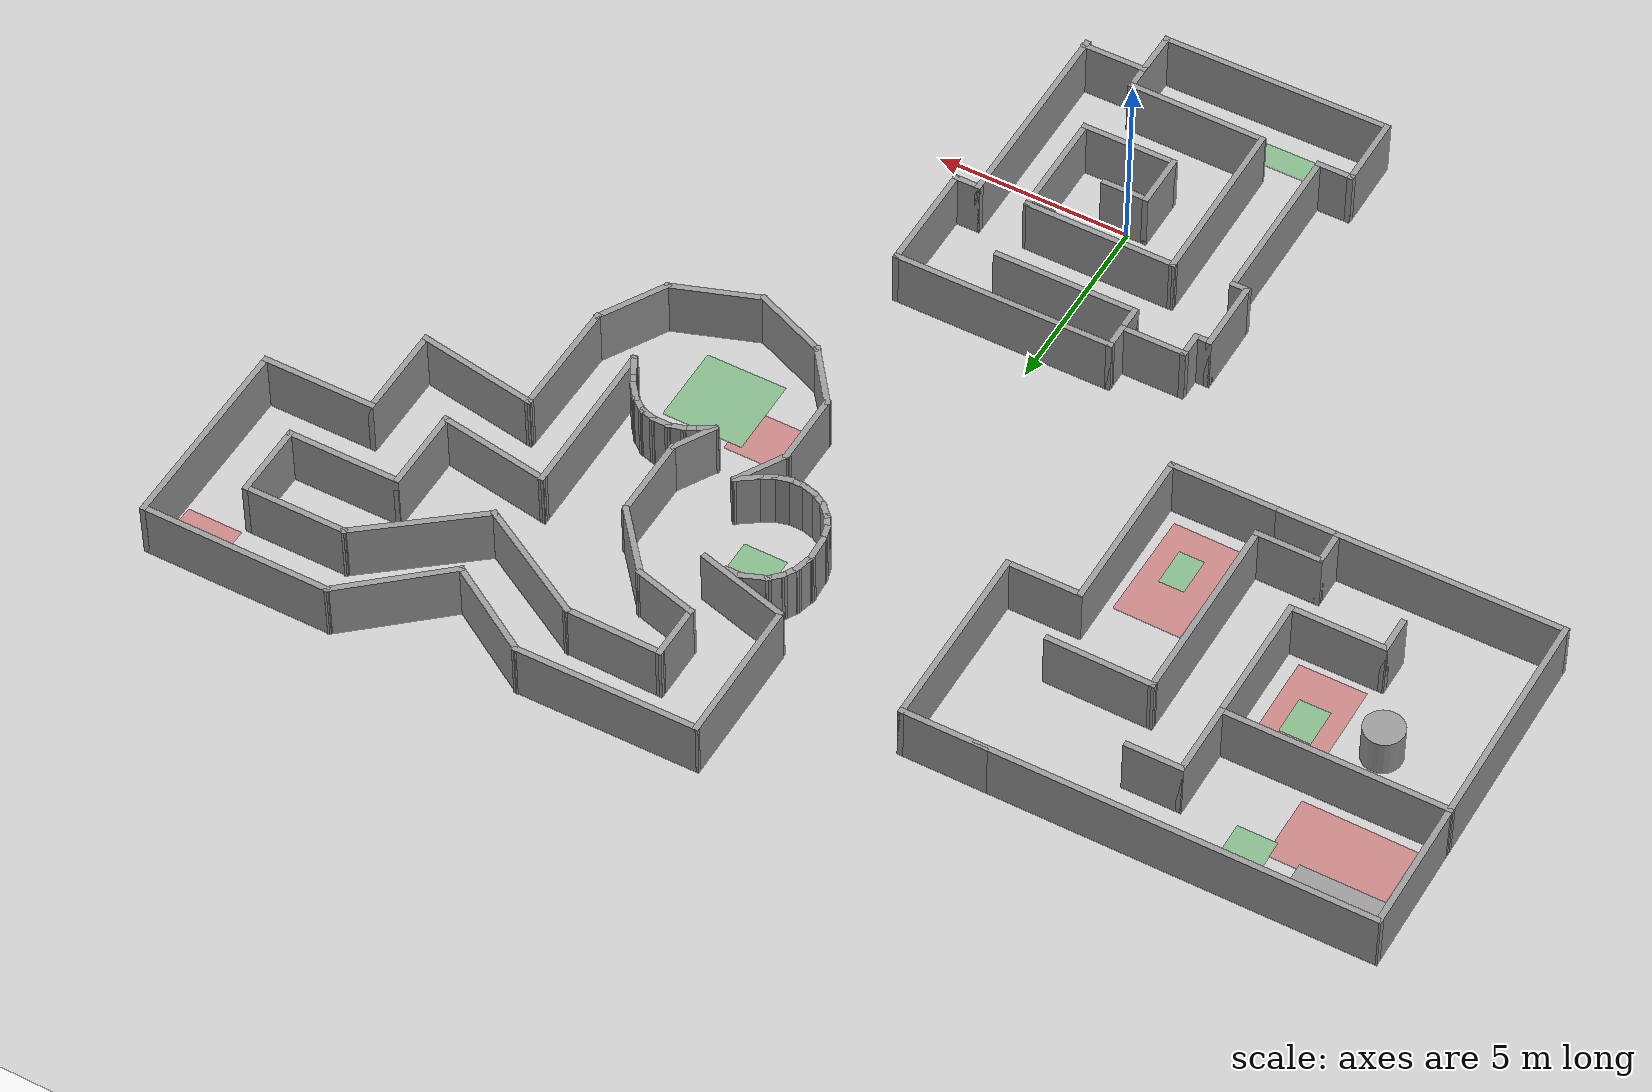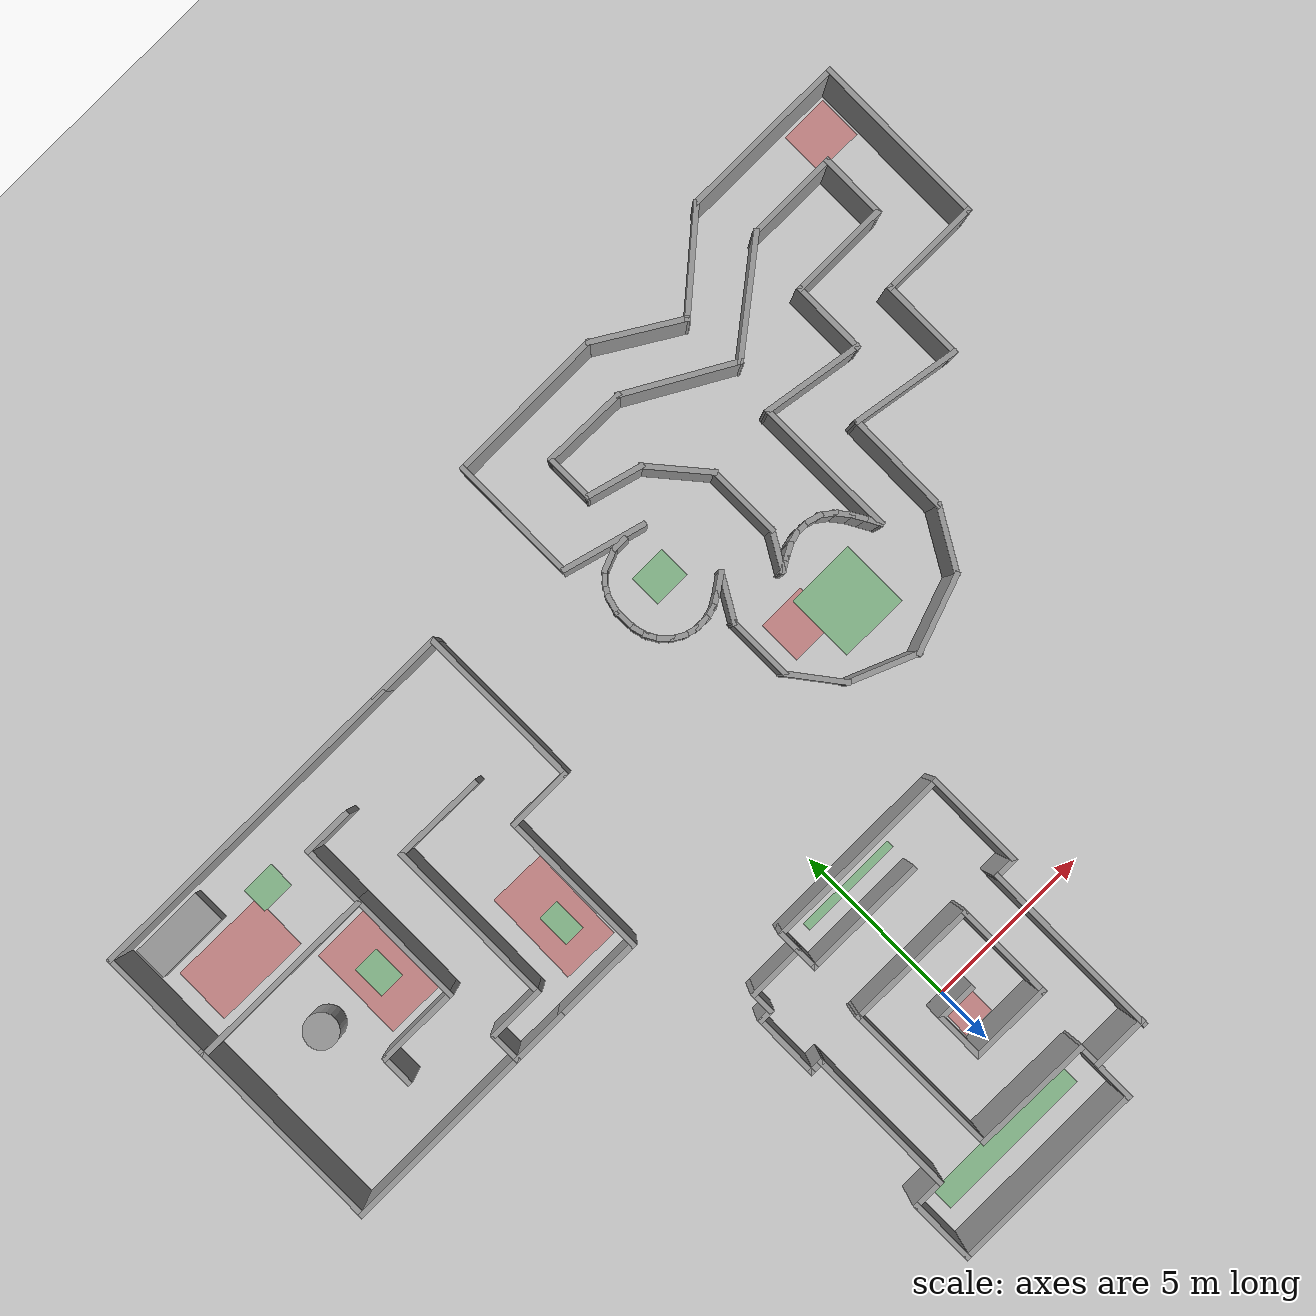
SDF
<sdf version="1.7">
 <world name="default">
  <light name="sun" type="directional">
   <pose>0 0 10 0 -0 0</pose>
   <diffuse>0.8 0.8 0.8 1</diffuse>
   <specular>0.2 0.2 0.2 1</specular>
   <attenuation>
    <range>1000</range>
    <constant>0.9</constant>
    <linear>0.01</linear>
    <quadratic>0.001</quadratic>
   </attenuation>
   <direction>-0.5 0.1 -0.9</direction>
   <spot><inner_angle>0</inner_angle><outer_angle>0</outer_angle><falloff>0</falloff></spot>
  </light>
  <model name="ground_plane">
   <static>1</static>
   <link name="link">
    <collision name="collision">
     <geometry><plane><normal>0 0 1</normal><size>100 100</size></plane></geometry>
     <surface>
      <contact><collide_bitmask>65535</collide_bitmask></contact>
      <friction><ode><mu>100</mu><mu2>50</mu2></ode></friction>
     </surface>
    </collision>
    <visual name="visual">
     <cast_shadows>0</cast_shadows>
     <geometry><plane><normal>0 0 1</normal><size>100 100</size></plane></geometry>
     <material>
      <script><uri>file://media/materials/scripts/gazebo.material</uri><name>Gazebo/Grey</name></script>
     </material>
    </visual>
   </link>
  </model>
  <gravity>0 0 -9.8</gravity>
  <magnetic_field>6e-06 2.3e-05 -4.2e-05</magnetic_field>
  <atmosphere type="adiabatic"/>
  <physics type="ode">
   <max_step_size>0.001</max_step_size>
   <real_time_factor>1</real_time_factor>
   <real_time_update_rate>1000</real_time_update_rate>
  </physics>
  <scene><ambient>0.4 0.4 0.4 1</ambient><background>0.7 0.7 0.7 1</background><shadows>1</shadows></scene>
  <spherical_coordinates>
   <surface_model>EARTH_WGS84</surface_model>
   <latitude_deg>0</latitude_deg>
   <longitude_deg>0</longitude_deg>
   <elevation>0</elevation>
   <heading_deg>0</heading_deg>
  </spherical_coordinates>
  <model name="map_1">
   <stepLimit>500</stepLimit>
   <pose>-0.281 -0.221428 0 0 -0 0</pose>
   <link name="Wall_1">
    <collision name="Wall_1_Collision">
     <geometry><box><size>4.5 0.15 1.5</size></box></geometry>
     <pose>0 0 0.75 0 -0 0</pose>
    </collision>
    <visual name="Wall_1_Visual">
     <pose>0 0 0.75 0 -0 0</pose>
     <geometry><box><size>4.5 0.15 1.5</size></box></geometry>
     <material>
      <script><uri>file://media/materials/scripts/gazebo.material</uri><name>Gazebo/Grey</name></script>
      <ambient>1 1 1 1</ambient>
     </material>
     <meta><layer>0</layer></meta>
    </visual>
    <pose>-3.175 -0.599572 0 0 -0 1.5708</pose>
   </link>
   <link name="Wall_16">
    <collision name="Wall_16_Collision">
     <geometry><box><size>1.75 0.15 1.5</size></box></geometry>
     <pose>0 0 0.75 0 -0 0</pose>
    </collision>
    <visual name="Wall_16_Visual">
     <pose>0 0 0.75 0 -0 0</pose>
     <geometry><box><size>1.75 0.15 1.5</size></box></geometry>
     <material>
      <script><uri>file://media/materials/scripts/gazebo.material</uri><name>Gazebo/Grey</name></script>
      <ambient>1 1 1 1</ambient>
     </material>
     <meta><layer>0</layer></meta>
    </visual>
    <pose>2.645 -3.48157 0 0 -0 3.14159</pose>
   </link>
   <link name="Wall_2">
    <collision name="Wall_2_Collision">
     <geometry><box><size>0.5 0.15 1.5</size></box></geometry>
     <pose>0 0 0.75 0 -0 0</pose>
    </collision>
    <visual name="Wall_2_Visual">
     <pose>0 0 0.75 0 -0 0</pose>
     <geometry><box><size>0.5 0.15 1.5</size></box></geometry>
     <material>
      <script><uri>file://media/materials/scripts/gazebo.material</uri><name>Gazebo/Grey</name></script>
      <ambient>1 1 1 1</ambient>
     </material>
     <meta><layer>0</layer></meta>
    </visual>
    <pose>-3.35 1.57543 0 0 -0 3.14159</pose>
   </link>
   <link name="Wall_25">
    <collision name="Wall_25_Collision">
     <geometry><box><size>4.00007 0.15 1.5</size></box></geometry>
     <pose>0 0 0.75 0 -0 0</pose>
    </collision>
    <visual name="Wall_25_Visual">
     <pose>0 0 0.75 0 -0 0</pose>
     <geometry><box><size>4.00007 0.15 1.5</size></box></geometry>
     <material>
      <script><uri>file://media/materials/scripts/gazebo.material</uri><name>Gazebo/Grey</name></script>
      <ambient>1 1 1 1</ambient>
     </material>
     <meta><layer>0</layer></meta>
    </visual>
    <pose>0.249 1.70643 0 0 -0 -0.006234</pose>
   </link>
   <link name="Wall_26">
    <collision name="Wall_26_Collision">
     <geometry><box><size>3 0.15 1.5</size></box></geometry>
     <pose>0 0 0.75 0 -0 0</pose>
    </collision>
    <visual name="Wall_26_Visual">
     <pose>0 0 0.75 0 -0 0</pose>
     <geometry><box><size>3 0.15 1.5</size></box></geometry>
     <material>
      <script><uri>file://media/materials/scripts/gazebo.material</uri><name>Gazebo/Grey</name></script>
      <ambient>1 1 1 1</ambient>
     </material>
     <meta><layer>0</layer></meta>
    </visual>
    <pose>2.174 0.269428 0 0 -0 -1.5708</pose>
   </link>
   <link name="Wall_27">
    <collision name="Wall_27_Collision">
     <geometry><box><size>2.5 0.15 1.5</size></box></geometry>
     <pose>0 0 0.75 0 -0 0</pose>
    </collision>
    <visual name="Wall_27_Visual">
     <pose>0 0 0.75 0 -0 0</pose>
     <geometry><box><size>2.5 0.15 1.5</size></box></geometry>
     <material>
      <script><uri>file://media/materials/scripts/gazebo.material</uri><name>Gazebo/Grey</name></script>
      <ambient>1 1 1 1</ambient>
     </material>
     <meta><layer>0</layer></meta>
    </visual>
    <pose>0.999 -1.15557 0 0 -0 3.14159</pose>
   </link>
   <link name="Wall_3">
    <collision name="Wall_3_Collision">
     <geometry><box><size>2 0.15 1.5</size></box></geometry>
     <pose>0 0 0.75 0 -0 0</pose>
    </collision>
    <visual name="Wall_3_Visual">
     <pose>0 0 0.75 0 -0 0</pose>
     <geometry><box><size>2 0.15 1.5</size></box></geometry>
     <material>
      <script><uri>file://media/materials/scripts/gazebo.material</uri><name>Gazebo/Grey</name></script>
      <ambient>1 1 1 1</ambient>
     </material>
     <meta><layer>0</layer></meta>
    </visual>
    <pose>-3.525 2.50043 0 0 -0 1.5708</pose>
   </link>
   <link name="Wall_31">
    <collision name="Wall_31_Collision">
     <geometry><box><size>3.64467 0.15 1.5</size></box></geometry>
     <pose>0 0 0.75 0 -0 0</pose>
    </collision>
    <visual name="Wall_31_Visual">
     <pose>0 0 0.75 0 -0 0</pose>
     <geometry><box><size>3.64467 0.15 1.5</size></box></geometry>
     <material>
      <script><uri>file://media/materials/scripts/gazebo.material</uri><name>Gazebo/Grey</name></script>
      <ambient>1 1 1 1</ambient>
     </material>
     <meta><layer>0</layer></meta>
    </visual>
    <pose>0.0975 -2.85407 0 0 -0 -0.015735</pose>
   </link>
   <link name="Wall_33">
    <collision name="Wall_33_Collision">
     <geometry><box><size>1 0.15 1.5</size></box></geometry>
     <pose>0 0 0.75 0 -0 0</pose>
    </collision>
    <visual name="Wall_33_Visual">
     <pose>0 0 0.75 0 -0 0</pose>
     <geometry><box><size>1 0.15 1.5</size></box></geometry>
     <material>
      <script><uri>file://media/materials/scripts/gazebo.material</uri><name>Gazebo/Grey</name></script>
      <ambient>1 1 1 1</ambient>
     </material>
     <meta><layer>0</layer></meta>
    </visual>
    <pose>-3.6 -2.77457 0 0 -0 3.14159</pose>
   </link>
   <link name="Wall_34">
    <collision name="Wall_34_Collision">
     <geometry><box><size>2 0.15 1.5</size></box></geometry>
     <pose>0 0 0.75 0 -0 0</pose>
    </collision>
    <visual name="Wall_34_Visual">
     <pose>0 0 0.75 0 -0 0</pose>
     <geometry><box><size>2 0.15 1.5</size></box></geometry>
     <material>
      <script><uri>file://media/materials/scripts/gazebo.material</uri><name>Gazebo/Grey</name></script>
      <ambient>1 1 1 1</ambient>
     </material>
     <meta><layer>0</layer></meta>
    </visual>
    <pose>-4.025 -3.69957 0 0 -0 -1.5708</pose>
   </link>
   <link name="Wall_35">
    <collision name="Wall_35_Collision">
     <geometry><box><size>6 0.15 1.5</size></box></geometry>
     <pose>0 0 0.75 0 -0 0</pose>
    </collision>
    <visual name="Wall_35_Visual">
     <pose>0 0 0.75 0 -0 0</pose>
     <geometry><box><size>6 0.15 1.5</size></box></geometry>
     <material>
      <script><uri>file://media/materials/scripts/gazebo.material</uri><name>Gazebo/Grey</name></script>
      <ambient>1 1 1 1</ambient>
     </material>
     <meta><layer>0</layer></meta>
    </visual>
    <pose>-1.1 -4.62457 0 0 -0 0</pose>
   </link>
   <link name="Wall_4">
    <collision name="Wall_4_Collision">
     <geometry><box><size>0.5 0.15 1.5</size></box></geometry>
     <pose>0 0 0.75 0 -0 0</pose>
    </collision>
    <visual name="Wall_4_Visual">
     <pose>0 0 0.75 0 -0 0</pose>
     <geometry><box><size>0.5 0.15 1.5</size></box></geometry>
     <material>
      <script><uri>file://media/materials/scripts/gazebo.material</uri><name>Gazebo/Grey</name></script>
      <ambient>1 1 1 1</ambient>
     </material>
     <meta><layer>0</layer></meta>
    </visual>
    <pose>-3.35 3.42543 0 0 -0 0</pose>
   </link>
   <link name="Wall_43">
    <collision name="Wall_43_Collision">
     <geometry><box><size>1.5 0.15 1.5</size></box></geometry>
     <pose>0 0 0.75 0 -0 0</pose>
    </collision>
    <visual name="Wall_43_Visual">
     <pose>0 0 0.75 0 -0 0</pose>
     <geometry><box><size>1.5 0.15 1.5</size></box></geometry>
     <material>
      <script><uri>file://media/materials/scripts/gazebo.material</uri><name>Gazebo/Grey</name></script>
      <ambient>1 1 1 1</ambient>
     </material>
     <meta><layer>0</layer></meta>
    </visual>
    <pose>-0.176 -0.480572 0 0 -0 1.5708</pose>
   </link>
   <link name="Wall_44">
    <collision name="Wall_44_Collision">
     <geometry><box><size>1.25 0.15 1.5</size></box></geometry>
     <pose>0 0 0.75 0 -0 0</pose>
    </collision>
    <visual name="Wall_44_Visual">
     <pose>0 0 0.75 0 -0 0</pose>
     <geometry><box><size>1.25 0.15 1.5</size></box></geometry>
     <material>
      <script><uri>file://media/materials/scripts/gazebo.material</uri><name>Gazebo/Grey</name></script>
      <ambient>1 1 1 1</ambient>
     </material>
     <meta><layer>0</layer></meta>
    </visual>
    <pose>0.374 0.194428 0 0 -0 0</pose>
   </link>
   <link name="Wall_49">
    <collision name="Wall_49_Collision">
     <geometry><box><size>4.69527 0.15 1.5</size></box></geometry>
     <pose>0 0 0.75 0 -0 0</pose>
    </collision>
    <visual name="Wall_49_Visual">
     <pose>0 0 0.75 0 -0 0</pose>
     <geometry><box><size>4.69527 0.15 1.5</size></box></geometry>
     <material>
      <script><uri>file://media/materials/scripts/gazebo.material</uri><name>Gazebo/Grey</name></script>
      <ambient>1 1 1 1</ambient>
     </material>
     <meta><layer>0</layer></meta>
    </visual>
    <pose>-1.663 -0.554072 0 0 -0 1.57652</pose>
   </link>
   <link name="Wall_5">
    <collision name="Wall_5_Collision">
     <geometry><box><size>0.75 0.15 1.5</size></box></geometry>
     <pose>0 0 0.75 0 -0 0</pose>
    </collision>
    <visual name="Wall_5_Visual">
     <pose>0 0 0.75 0 -0 0</pose>
     <geometry><box><size>0.75 0.15 1.5</size></box></geometry>
     <material>
      <script><uri>file://media/materials/scripts/gazebo.material</uri><name>Gazebo/Grey</name></script>
      <ambient>1 1 1 1</ambient>
     </material>
     <meta><layer>0</layer></meta>
    </visual>
    <pose>-3.175 3.72543 0 0 -0 1.5708</pose>
   </link>
   <link name="Wall_51">
    <collision name="Wall_51_Collision">
     <geometry><box><size>3.75 0.15 1.5</size></box></geometry>
     <pose>0 0 0.75 0 -0 0</pose>
    </collision>
    <visual name="Wall_51_Visual">
     <pose>0 0 0.75 0 -0 0</pose>
     <geometry><box><size>3.75 0.15 1.5</size></box></geometry>
     <material>
      <script><uri>file://media/materials/scripts/gazebo.material</uri><name>Gazebo/Grey</name></script>
      <ambient>1 1 1 1</ambient>
     </material>
     <meta><layer>0</layer></meta>
    </visual>
    <pose>0.225 3.42543 0 0 -0 0</pose>
   </link>
   <link name="Wall_57">
    <collision name="Wall_57_Collision">
     <geometry><box><size>0.75 0.15 1.5</size></box></geometry>
     <pose>0 0 0.75 0 -0 0</pose>
    </collision>
    <visual name="Wall_57_Visual">
     <pose>0 0 0.75 0 -0 0</pose>
     <geometry><box><size>0.75 0.15 1.5</size></box></geometry>
     <material>
      <script><uri>file://media/materials/scripts/gazebo.material</uri><name>Gazebo/Grey</name></script>
      <ambient>1 1 1 1</ambient>
     </material>
     <meta><layer>0</layer></meta>
    </visual>
    <pose>-1.575 4.32543 0 0 -0 1.5708</pose>
   </link>
   <link name="Wall_6">
    <collision name="Wall_6_Collision">
     <geometry><box><size>1.75 0.15 1.5</size></box></geometry>
     <pose>0 0 0.75 0 -0 0</pose>
    </collision>
    <visual name="Wall_6_Visual">
     <pose>0 0 0.75 0 -0 0</pose>
     <geometry><box><size>1.75 0.15 1.5</size></box></geometry>
     <material>
      <script><uri>file://media/materials/scripts/gazebo.material</uri><name>Gazebo/Grey</name></script>
      <ambient>1 1 1 1</ambient>
     </material>
     <meta><layer>0</layer></meta>
    </visual>
    <pose>-2.375 4.02543 0 0 -0 0</pose>
   </link>
   <link name="Wall_62">
    <collision name="Wall_62_Collision">
     <geometry><box><size>5.75 0.15 1.5</size></box></geometry>
     <pose>0 0 0.75 0 -0 0</pose>
    </collision>
    <visual name="Wall_62_Visual">
     <pose>0 0 0.75 0 -0 0</pose>
     <geometry><box><size>5.75 0.15 1.5</size></box></geometry>
     <material>
      <script><uri>file://media/materials/scripts/gazebo.material</uri><name>Gazebo/Grey</name></script>
      <ambient>1 1 1 1</ambient>
     </material>
     <meta><layer>0</layer></meta>
    </visual>
    <pose>1.225 4.62543 0 0 -0 0</pose>
   </link>
   <link name="Wall_63">
    <collision name="Wall_63_Collision">
     <geometry><box><size>3 0.15 1.5</size></box></geometry>
     <pose>0 0 0.75 0 -0 0</pose>
    </collision>
    <visual name="Wall_63_Visual">
     <pose>0 0 0.75 0 -0 0</pose>
     <geometry><box><size>3 0.15 1.5</size></box></geometry>
     <material>
      <script><uri>file://media/materials/scripts/gazebo.material</uri><name>Gazebo/Grey</name></script>
      <ambient>1 1 1 1</ambient>
     </material>
     <meta><layer>0</layer></meta>
    </visual>
    <pose>4.025 3.20043 0 0 -0 -1.5708</pose>
   </link>
   <link name="Wall_67">
    <collision name="Wall_67_Collision">
     <geometry><box><size>0.75 0.15 1.5</size></box></geometry>
     <pose>0 0 0.75 0 -0 0</pose>
    </collision>
    <visual name="Wall_67_Visual">
     <pose>0 0 0.75 0 -0 0</pose>
     <geometry><box><size>0.75 0.15 1.5</size></box></geometry>
     <material>
      <script><uri>file://media/materials/scripts/gazebo.material</uri><name>Gazebo/Grey</name></script>
      <ambient>1 1 1 1</ambient>
     </material>
     <meta><layer>0</layer></meta>
    </visual>
    <pose>3.725 1.77543 0 0 -0 3.14159</pose>
   </link>
   <link name="Wall_68">
    <collision name="Wall_68_Collision">
     <geometry><box><size>5.5 0.15 1.5</size></box></geometry>
     <pose>0 0 0.75 0 -0 0</pose>
    </collision>
    <visual name="Wall_68_Visual">
     <pose>0 0 0.75 0 -0 0</pose>
     <geometry><box><size>5.5 0.15 1.5</size></box></geometry>
     <material>
      <script><uri>file://media/materials/scripts/gazebo.material</uri><name>Gazebo/Grey</name></script>
      <ambient>1 1 1 1</ambient>
     </material>
     <meta><layer>0</layer></meta>
    </visual>
    <pose>3.425 -0.899572 0 0 -0 -1.5708</pose>
   </link>
   <link name="Wall_7">
    <collision name="Wall_7_Collision">
     <geometry><box><size>0.75 0.15 1.5</size></box></geometry>
     <pose>0 0 0.75 0 -0 0</pose>
    </collision>
    <visual name="Wall_7_Visual">
     <pose>0 0 0.75 0 -0 0</pose>
     <geometry><box><size>0.75 0.15 1.5</size></box></geometry>
     <material>
      <script><uri>file://media/materials/scripts/gazebo.material</uri><name>Gazebo/Grey</name></script>
      <ambient>1 1 1 1</ambient>
     </material>
     <meta><layer>0</layer></meta>
    </visual>
    <pose>-1.575 3.72543 0 0 -0 -1.5708</pose>
   </link>
   <link name="Wall_73">
    <collision name="Wall_73_Collision">
     <geometry><box><size>1.89312 0.15 1.5</size></box></geometry>
     <pose>0 0 0.75 0 -0 0</pose>
    </collision>
    <visual name="Wall_73_Visual">
     <pose>0 0 0.75 0 -0 0</pose>
     <geometry><box><size>1.89312 0.15 1.5</size></box></geometry>
     <material>
      <script><uri>file://media/materials/scripts/gazebo.material</uri><name>Gazebo/Grey</name></script>
      <ambient>1 1 1 1</ambient>
     </material>
     <meta><layer>0</layer></meta>
    </visual>
    <pose>1.835 -3.75307 0 0 -0 -1.58227</pose>
   </link>
   <static>1</static>
  </model>
  <model name="map_1_spawn">
   <link name="spawn_1_a">
    <inertial>
     <mass>0.142312</mass>
     <inertia>
      <ixx>0.00473908</ixx>
      <ixy>0</ixy>
      <ixz>0</ixz>
      <iyy>0.271176</iyy>
      <iyz>0</iyz>
      <izz>0.275862</izz>
     </inertia>
    </inertial>
    <pose>-0.871908 -3.85609 0 0 -0 0</pose>
    <gravity>0</gravity>
    <visual name="visual">
     <geometry><box><size>4.78162 0.630375 0.047285</size></box></geometry>
     <material>
      <lighting>1</lighting>
      <script><uri>file://media/materials/scripts/gazebo.material</uri><name>Gazebo/Green</name></script>
      <shader type="pixel"><normal_map>__default__</normal_map></shader>
      <ambient>0 1 0 1</ambient>
      <diffuse>0 1 0 1</diffuse>
      <specular>0.1 0.1 0.1 1</specular>
      <emissive>0 0 0 1</emissive>
     </material>
     <transparency>0.6</transparency>
    </visual>
   </link>
   <link name="spawn_1_b">
    <spawnThreshold>15%</spawnThreshold>
    <inertial>
     <mass>0.142312</mass>
     <inertia>
      <ixx>0.00473908</ixx>
      <ixy>0</ixy>
      <ixz>0</ixz>
      <iyy>0.271176</iyy>
      <iyz>0</iyz>
      <izz>0.275862</izz>
     </inertia>
    </inertial>
    <pose>0.871907 3.85609 0 0 -0 0</pose>
    <gravity>0</gravity>
    <visual name="visual">
     <geometry><box><size>3.15894 0.222869 0.047285</size></box></geometry>
     <material>
      <lighting>1</lighting>
      <script><uri>file://media/materials/scripts/gazebo.material</uri><name>Gazebo/Green</name></script>
      <shader type="pixel"><normal_map>__default__</normal_map></shader>
      <ambient>0 1 0 1</ambient>
      <diffuse>0 1 0 1</diffuse>
      <specular>0.1 0.1 0.1 1</specular>
      <emissive>0 0 0 1</emissive>
     </material>
     <transparency>0.6</transparency>
    </visual>
   </link>
   <static>1</static>
   <pose>-0.620352 -0.06954 0 0 -0 0</pose>
  </model>
  <model name="map_1_target">
   <link name="target_1">
    <inertial>
     <mass>0.0166533</mass>
     <inertia>
      <ixx>0.00184915</ixx>
      <ixy>0</ixy>
      <ixz>0</ixz>
      <iyy>0.00125521</iyy>
      <iyz>0</iyz>
      <izz>0.00310372</izz>
     </inertia>
    </inertial>
    <gravity>0</gravity>
    <visual name="visual">
     <geometry><box><size>0.95092 1.15422 0.015138</size></box></geometry>
     <material>
      <lighting>1</lighting>
      <script><uri>file://media/materials/scripts/gazebo.material</uri><name>Gazebo/Red</name></script>
      <shader type="pixel"><normal_map>__default__</normal_map></shader>
      <ambient>1 0 0 1</ambient>
      <diffuse>1 0 0 1</diffuse>
      <specular>0.1 0.1 0.1 1</specular>
      <emissive>0 0 0 1</emissive>
     </material>
     <transparency>0.6</transparency>
    </visual>
   </link>
   <static>1</static>
   <pose>0.147086 -0.699277 0.010111 0 -0 0</pose>
  </model>
  <model name="map_2">
   <stepLimit>500</stepLimit>
   <pose>7.75806 13.2212 0 0 -0 0</pose>
   <link name="Wall_10">
    <collision name="Wall_10_Collision">
     <geometry><box><size>2.75 0.15 1.5</size></box></geometry>
     <pose>0 0 0.75 0 -0 0</pose>
    </collision>
    <visual name="Wall_10_Visual">
     <pose>0 0 0.75 0 -0 0</pose>
     <geometry><box><size>2.75 0.15 1.5</size></box></geometry>
     <material>
      <script><uri>file://media/materials/scripts/gazebo.material</uri><name>Gazebo/Grey</name></script>
      <ambient>1 1 1 1</ambient>
     </material>
     <meta><layer>0</layer></meta>
    </visual>
    <pose>4.01324 4.53292 0 0 -0 3.14159</pose>
   </link>
   <link name="Wall_100">
    <collision name="Wall_100_Collision">
     <geometry><box><size>0.5 0.15 1.5</size></box></geometry>
     <pose>0 0 0.75 0 -0 0</pose>
    </collision>
    <visual name="Wall_100_Visual">
     <pose>0 0 0.75 0 -0 0</pose>
     <geometry><box><size>0.5 0.15 1.5</size></box></geometry>
     <material>
      <script><uri>file://media/materials/scripts/gazebo.material</uri><name>Gazebo/Grey</name></script>
      <ambient>1 1 1 1</ambient>
     </material>
     <meta><layer>0</layer></meta>
    </visual>
    <pose>-2.19576 -1.78658 0 0 -0 0.262995</pose>
   </link>
   <link name="Wall_101">
    <collision name="Wall_101_Collision">
     <geometry><box><size>0.546939 0.15 1.5</size></box></geometry>
     <pose>0 0 0.75 0 -0 0</pose>
    </collision>
    <visual name="Wall_101_Visual">
     <pose>0 0 0.75 0 -0 0</pose>
     <geometry><box><size>0.546939 0.15 1.5</size></box></geometry>
     <material>
      <script><uri>file://media/materials/scripts/gazebo.material</uri><name>Gazebo/Grey</name></script>
      <ambient>1 1 1 1</ambient>
     </material>
     <meta><layer>0</layer></meta>
    </visual>
    <pose>-1.82826 -1.74408 0 0 -0 -0.015112</pose>
   </link>
   <link name="Wall_102">
    <collision name="Wall_102_Collision">
     <geometry><box><size>0.5 0.15 1.5</size></box></geometry>
     <pose>0 0 0.75 0 -0 0</pose>
    </collision>
    <visual name="Wall_102_Visual">
     <pose>0 0 0.75 0 -0 0</pose>
     <geometry><box><size>0.5 0.15 1.5</size></box></geometry>
     <material>
      <script><uri>file://media/materials/scripts/gazebo.material</uri><name>Gazebo/Grey</name></script>
      <ambient>1 1 1 1</ambient>
     </material>
     <meta><layer>0</layer></meta>
    </visual>
    <pose>-1.46076 -1.79258 0 0 -0 -0.262995</pose>
   </link>
   <link name="Wall_103">
    <collision name="Wall_103_Collision">
     <geometry><box><size>0.544934 0.15 1.5</size></box></geometry>
     <pose>0 0 0.75 0 -0 0</pose>
    </collision>
    <visual name="Wall_103_Visual">
     <pose>0 0 0.75 0 -0 0</pose>
     <geometry><box><size>0.544934 0.15 1.5</size></box></geometry>
     <material>
      <script><uri>file://media/materials/scripts/gazebo.material</uri><name>Gazebo/Grey</name></script>
      <ambient>1 1 1 1</ambient>
     </material>
     <meta><layer>0</layer></meta>
    </visual>
    <pose>-1.13276 -1.95558 0 0 -0 -0.63642</pose>
   </link>
   <link name="Wall_104">
    <collision name="Wall_104_Collision">
     <geometry><box><size>0.590386 0.15 1.5</size></box></geometry>
     <pose>0 0 0.75 0 -0 0</pose>
    </collision>
    <visual name="Wall_104_Visual">
     <pose>0 0 0.75 0 -0 0</pose>
     <geometry><box><size>0.590386 0.15 1.5</size></box></geometry>
     <material>
      <script><uri>file://media/materials/scripts/gazebo.material</uri><name>Gazebo/Grey</name></script>
      <ambient>1 1 1 1</ambient>
     </material>
     <meta><layer>0</layer></meta>
    </visual>
    <pose>-0.837762 -2.24608 0 0 -0 -0.904572</pose>
   </link>
   <link name="Wall_105">
    <collision name="Wall_105_Collision">
     <geometry><box><size>0.5 0.15 1.5</size></box></geometry>
     <pose>0 0 0.75 0 -0 0</pose>
    </collision>
    <visual name="Wall_105_Visual">
     <pose>0 0 0.75 0 -0 0</pose>
     <geometry><box><size>0.5 0.15 1.5</size></box></geometry>
     <material>
      <script><uri>file://media/materials/scripts/gazebo.material</uri><name>Gazebo/Grey</name></script>
      <ambient>1 1 1 1</ambient>
     </material>
     <meta><layer>0</layer></meta>
    </visual>
    <pose>-0.614262 -2.57058 0 0 -0 -1.04704</pose>
   </link>
   <link name="Wall_106">
    <collision name="Wall_106_Collision">
     <geometry><box><size>0.581498 0.15 1.5</size></box></geometry>
     <pose>0 0 0.75 0 -0 0</pose>
    </collision>
    <visual name="Wall_106_Visual">
     <pose>0 0 0.75 0 -0 0</pose>
     <geometry><box><size>0.581498 0.15 1.5</size></box></geometry>
     <material>
      <script><uri>file://media/materials/scripts/gazebo.material</uri><name>Gazebo/Grey</name></script>
      <ambient>1 1 1 1</ambient>
     </material>
     <meta><layer>0</layer></meta>
    </visual>
    <pose>-0.422762 -2.91108 0 0 -0 -1.06775</pose>
   </link>
   <link name="Wall_12">
    <collision name="Wall_12_Collision">
     <geometry><box><size>3.54164 0.15 1.5</size></box></geometry>
     <pose>0 0 0.75 0 -0 0</pose>
    </collision>
    <visual name="Wall_12_Visual">
     <pose>0 0 0.75 0 -0 0</pose>
     <geometry><box><size>3.54164 0.15 1.5</size></box></geometry>
     <material>
      <script><uri>file://media/materials/scripts/gazebo.material</uri><name>Gazebo/Grey</name></script>
      <ambient>1 1 1 1</ambient>
     </material>
     <meta><layer>0</layer></meta>
    </visual>
    <pose>1.38174 3.48292 0 0 -0 0.667741</pose>
   </link>
   <link name="Wall_14">
    <collision name="Wall_14_Collision">
     <geometry><box><size>3.42797 0.15 1.5</size></box></geometry>
     <pose>0 0 0.75 0 -0 0</pose>
    </collision>
    <visual name="Wall_14_Visual">
     <pose>0 0 0.75 0 -0 0</pose>
     <geometry><box><size>3.42797 0.15 1.5</size></box></geometry>
     <material>
      <script><uri>file://media/materials/scripts/gazebo.material</uri><name>Gazebo/Grey</name></script>
      <ambient>1 1 1 1</ambient>
     </material>
     <meta><layer>0</layer></meta>
    </visual>
    <pose>-1.37776 3.23742 0 0 -0 -0.513054</pose>
   </link>
   <link name="Wall_16">
    <collision name="Wall_16_Collision">
     <geometry><box><size>2.56379 0.15 1.5</size></box></geometry>
     <pose>0 0 0.75 0 -0 0</pose>
    </collision>
    <visual name="Wall_16_Visual">
     <pose>0 0 0.75 0 -0 0</pose>
     <geometry><box><size>2.56379 0.15 1.5</size></box></geometry>
     <material>
      <script><uri>file://media/materials/scripts/gazebo.material</uri><name>Gazebo/Grey</name></script>
      <ambient>1 1 1 1</ambient>
     </material>
     <meta><layer>0</layer></meta>
    </visual>
    <pose>-4.01276 4.06192 0 0 -0 -0.016568</pose>
   </link>
   <link name="Wall_18">
    <collision name="Wall_18_Collision">
     <geometry><box><size>1.5 0.15 1.5</size></box></geometry>
     <pose>0 0 0.75 0 -0 0</pose>
    </collision>
    <visual name="Wall_18_Visual">
     <pose>0 0 0.75 0 -0 0</pose>
     <geometry><box><size>1.5 0.15 1.5</size></box></geometry>
     <material>
      <script><uri>file://media/materials/scripts/gazebo.material</uri><name>Gazebo/Grey</name></script>
      <ambient>1 1 1 1</ambient>
     </material>
     <meta><layer>0</layer></meta>
    </visual>
    <pose>-5.21976 3.40692 0 0 -0 -1.5708</pose>
   </link>
   <link name="Wall_19">
    <collision name="Wall_19_Collision">
     <geometry><box><size>1.75 0.15 1.5</size></box></geometry>
     <pose>0 0 0.75 0 -0 0</pose>
    </collision>
    <visual name="Wall_19_Visual">
     <pose>0 0 0.75 0 -0 0</pose>
     <geometry><box><size>1.75 0.15 1.5</size></box></geometry>
     <material>
      <script><uri>file://media/materials/scripts/gazebo.material</uri><name>Gazebo/Grey</name></script>
      <ambient>1 1 1 1</ambient>
     </material>
     <meta><layer>0</layer></meta>
    </visual>
    <pose>-4.44676 2.52492 0 0 -0 -0.261649</pose>
   </link>
   <link name="Wall_2">
    <collision name="Wall_2_Collision">
     <geometry><box><size>4.27213 0.15 1.5</size></box></geometry>
     <pose>0 0 0.75 0 -0 0</pose>
    </collision>
    <visual name="Wall_2_Visual">
     <pose>0 0 0.75 0 -0 0</pose>
     <geometry><box><size>4.27213 0.15 1.5</size></box></geometry>
     <material>
      <script><uri>file://media/materials/scripts/gazebo.material</uri><name>Gazebo/Grey</name></script>
      <ambient>1 1 1 1</ambient>
     </material>
     <meta><layer>0</layer></meta>
    </visual>
    <pose>-0.335262 -1.03908 0 0 -0 1.5788</pose>
   </link>
   <link name="Wall_21">
    <collision name="Wall_21_Collision">
     <geometry><box><size>2.05434 0.15 1.5</size></box></geometry>
     <pose>0 0 0.75 0 -0 0</pose>
    </collision>
    <visual name="Wall_21_Visual">
     <pose>0 0 0.75 0 -0 0</pose>
     <geometry><box><size>2.05434 0.15 1.5</size></box></geometry>
     <material>
      <script><uri>file://media/materials/scripts/gazebo.material</uri><name>Gazebo/Grey</name></script>
      <ambient>1 1 1 1</ambient>
     </material>
     <meta><layer>0</layer></meta>
    </visual>
    <pose>-3.05876 1.59092 0 0 -0 2.27293</pose>
   </link>
   <link name="Wall_42">
    <collision name="Wall_42_Collision">
     <geometry><box><size>2.25 0.15 1.5</size></box></geometry>
     <pose>0 0 0.75 0 -0 0</pose>
    </collision>
    <visual name="Wall_42_Visual">
     <pose>0 0 0.75 0 -0 0</pose>
     <geometry><box><size>2.25 0.15 1.5</size></box></geometry>
     <material>
      <script><uri>file://media/materials/scripts/gazebo.material</uri><name>Gazebo/Grey</name></script>
      <ambient>1 1 1 1</ambient>
     </material>
     <meta><layer>0</layer></meta>
    </visual>
    <pose>-2.44376 -0.186078 0 0 -0 -1.5708</pose>
   </link>
   <link name="Wall_43">
    <collision name="Wall_43_Collision">
     <geometry><box><size>1.25 0.15 1.5</size></box></geometry>
     <pose>0 0 0.75 0 -0 0</pose>
    </collision>
    <visual name="Wall_43_Visual">
     <pose>0 0 0.75 0 -0 0</pose>
     <geometry><box><size>1.25 0.15 1.5</size></box></geometry>
     <material>
      <script><uri>file://media/materials/scripts/gazebo.material</uri><name>Gazebo/Grey</name></script>
      <ambient>1 1 1 1</ambient>
     </material>
     <meta><layer>0</layer></meta>
    </visual>
    <pose>-2.71876 -1.71208 0 0 -0 -2.09468</pose>
   </link>
   <link name="Wall_45">
    <collision name="Wall_45_Collision">
     <geometry><box><size>1.5 0.15 1.5</size></box></geometry>
     <pose>0 0 0.75 0 -0 0</pose>
    </collision>
    <visual name="Wall_45_Visual">
     <pose>0 0 0.75 0 -0 0</pose>
     <geometry><box><size>1.5 0.15 1.5</size></box></geometry>
     <material>
      <script><uri>file://media/materials/scripts/gazebo.material</uri><name>Gazebo/Grey</name></script>
      <ambient>1 1 1 1</ambient>
     </material>
     <meta><layer>0</layer></meta>
    </visual>
    <pose>-4.48526 -1.67358 0 0 -0 -2.09444</pose>
   </link>
   <link name="Wall_46">
    <collision name="Wall_46_Collision">
     <geometry><box><size>2 0.15 1.5</size></box></geometry>
     <pose>0 0 0.75 0 -0 0</pose>
    </collision>
    <visual name="Wall_46_Visual">
     <pose>0 0 0.75 0 -0 0</pose>
     <geometry><box><size>2 0.15 1.5</size></box></geometry>
     <material>
      <script><uri>file://media/materials/scripts/gazebo.material</uri><name>Gazebo/Grey</name></script>
      <ambient>1 1 1 1</ambient>
     </material>
     <meta><layer>0</layer></meta>
    </visual>
    <pose>-4.82276 -3.18308 0 0 -0 -1.5708</pose>
   </link>
   <link name="Wall_48">
    <collision name="Wall_48_Collision">
     <geometry><box><size>1.79931 0.15 1.5</size></box></geometry>
     <pose>0 0 0.75 0 -0 0</pose>
    </collision>
    <visual name="Wall_48_Visual">
     <pose>0 0 0.75 0 -0 0</pose>
     <geometry><box><size>1.79931 0.15 1.5</size></box></geometry>
     <material>
      <script><uri>file://media/materials/scripts/gazebo.material</uri><name>Gazebo/Grey</name></script>
      <ambient>1 1 1 1</ambient>
     </material>
     <meta><layer>0</layer></meta>
    </visual>
    <pose>-4.32126 -4.76258 0 0 -0 2.22461</pose>
   </link>
   <link name="Wall_5">
    <collision name="Wall_5_Collision">
     <geometry><box><size>2.99933 0.15 1.5</size></box></geometry>
     <pose>0 0 0.75 0 -0 0</pose>
    </collision>
    <visual name="Wall_5_Visual">
     <pose>0 0 0.75 0 -0 0</pose>
     <geometry><box><size>2.99933 0.15 1.5</size></box></geometry>
     <material>
      <script><uri>file://media/materials/scripts/gazebo.material</uri><name>Gazebo/Grey</name></script>
      <ambient>1 1 1 1</ambient>
     </material>
     <meta><layer>0</layer></meta>
    </visual>
    <pose>1.05574 0.802422 0 0 -0 2.98689</pose>
   </link>
   <link name="Wall_51">
    <collision name="Wall_51_Collision">
     <geometry><box><size>2.13517 0.15 1.5</size></box></geometry>
     <pose>0 0 0.75 0 -0 0</pose>
    </collision>
    <visual name="Wall_51_Visual">
     <pose>0 0 0.75 0 -0 0</pose>
     <geometry><box><size>2.13517 0.15 1.5</size></box></geometry>
     <material>
      <script><uri>file://media/materials/scripts/gazebo.material</uri><name>Gazebo/Grey</name></script>
      <ambient>1 1 1 1</ambient>
     </material>
     <meta><layer>0</layer></meta>
    </visual>
    <pose>-2.90126 -5.79458 0 0 -0 2.75164</pose>
   </link>
   <link name="Wall_53">
    <collision name="Wall_53_Collision">
     <geometry><box><size>2 0.15 1.5</size></box></geometry>
     <pose>0 0 0.75 0 -0 0</pose>
    </collision>
    <visual name="Wall_53_Visual">
     <pose>0 0 0.75 0 -0 0</pose>
     <geometry><box><size>2 0.15 1.5</size></box></geometry>
     <material>
      <script><uri>file://media/materials/scripts/gazebo.material</uri><name>Gazebo/Grey</name></script>
      <ambient>1 1 1 1</ambient>
     </material>
     <meta><layer>0</layer></meta>
    </visual>
    <pose>0.603738 -4.61208 0 0 -0 -2.09443</pose>
   </link>
   <link name="Wall_54">
    <collision name="Wall_54_Collision">
     <geometry><box><size>2.40606 0.15 1.5</size></box></geometry>
     <pose>0 0 0.75 0 -0 0</pose>
    </collision>
    <visual name="Wall_54_Visual">
     <pose>0 0 0.75 0 -0 0</pose>
     <geometry><box><size>2.40606 0.15 1.5</size></box></geometry>
     <material>
      <script><uri>file://media/materials/scripts/gazebo.material</uri><name>Gazebo/Grey</name></script>
      <ambient>1 1 1 1</ambient>
     </material>
     <meta><layer>0</layer></meta>
    </visual>
    <pose>-0.920762 -5.79258 0 0 -0 -2.79839</pose>
   </link>
   <link name="Wall_56">
    <collision name="Wall_56_Collision">
     <geometry><box><size>3.16414 0.15 1.5</size></box></geometry>
     <pose>0 0 0.75 0 -0 0</pose>
    </collision>
    <visual name="Wall_56_Visual">
     <pose>0 0 0.75 0 -0 0</pose>
     <geometry><box><size>3.16414 0.15 1.5</size></box></geometry>
     <material>
      <script><uri>file://media/materials/scripts/gazebo.material</uri><name>Gazebo/Grey</name></script>
      <ambient>1 1 1 1</ambient>
     </material>
     <meta><layer>0</layer></meta>
    </visual>
    <pose>1.08274 -2.30408 0 0 -0 1.55985</pose>
   </link>
   <link name="Wall_61">
    <collision name="Wall_61_Collision">
     <geometry><box><size>3.23875 0.15 1.5</size></box></geometry>
     <pose>0 0 0.75 0 -0 0</pose>
    </collision>
    <visual name="Wall_61_Visual">
     <pose>0 0 0.75 0 -0 0</pose>
     <geometry><box><size>3.23875 0.15 1.5</size></box></geometry>
     <material>
      <script><uri>file://media/materials/scripts/gazebo.material</uri><name>Gazebo/Grey</name></script>
      <ambient>1 1 1 1</ambient>
     </material>
     <meta><layer>0</layer></meta>
    </visual>
    <pose>2.62424 -1.04158 0 0 -0 2.98262</pose>
   </link>
   <link name="Wall_63">
    <collision name="Wall_63_Collision">
     <geometry><box><size>2.5 0.15 1.5</size></box></geometry>
     <pose>0 0 0.75 0 -0 0</pose>
    </collision>
    <visual name="Wall_63_Visual">
     <pose>0 0 0.75 0 -0 0</pose>
     <geometry><box><size>2.5 0.15 1.5</size></box></geometry>
     <material>
      <script><uri>file://media/materials/scripts/gazebo.material</uri><name>Gazebo/Grey</name></script>
      <ambient>1 1 1 1</ambient>
     </material>
     <meta><layer>0</layer></meta>
    </visual>
    <pose>4.14924 -0.111078 0 0 -0 1.5708</pose>
   </link>
   <link name="Wall_64">
    <collision name="Wall_64_Collision">
     <geometry><box><size>3 0.15 1.5</size></box></geometry>
     <pose>0 0 0.75 0 -0 0</pose>
    </collision>
    <visual name="Wall_64_Visual">
     <pose>0 0 0.75 0 -0 0</pose>
     <geometry><box><size>3 0.15 1.5</size></box></geometry>
     <material>
      <script><uri>file://media/materials/scripts/gazebo.material</uri><name>Gazebo/Grey</name></script>
      <ambient>1 1 1 1</ambient>
     </material>
     <meta><layer>0</layer></meta>
    </visual>
    <pose>5.57424 1.06392 0 0 -0 0</pose>
   </link>
   <link name="Wall_65">
    <collision name="Wall_65_Collision">
     <geometry><box><size>5.25 0.15 1.5</size></box></geometry>
     <pose>0 0 0.75 0 -0 0</pose>
    </collision>
    <visual name="Wall_65_Visual">
     <pose>0 0 0.75 0 -0 0</pose>
     <geometry><box><size>5.25 0.15 1.5</size></box></geometry>
     <material>
      <script><uri>file://media/materials/scripts/gazebo.material</uri><name>Gazebo/Grey</name></script>
      <ambient>1 1 1 1</ambient>
     </material>
     <meta><layer>0</layer></meta>
    </visual>
    <pose>6.99924 3.61392 0 0 -0 1.5708</pose>
   </link>
   <link name="Wall_66">
    <collision name="Wall_66_Collision">
     <geometry><box><size>5 0.15 1.5</size></box></geometry>
     <pose>0 0 0.75 0 -0 0</pose>
    </collision>
    <visual name="Wall_66_Visual">
     <pose>0 0 0.75 0 -0 0</pose>
     <geometry><box><size>5 0.15 1.5</size></box></geometry>
     <material>
      <script><uri>file://media/materials/scripts/gazebo.material</uri><name>Gazebo/Grey</name></script>
      <ambient>1 1 1 1</ambient>
     </material>
     <meta><layer>0</layer></meta>
    </visual>
    <pose>4.57424 6.16392 0 0 -0 3.14159</pose>
   </link>
   <link name="Wall_68">
    <collision name="Wall_68_Collision">
     <geometry><box><size>3.17756 0.15 1.5</size></box></geometry>
     <pose>0 0 0.75 0 -0 0</pose>
    </collision>
    <visual name="Wall_68_Visual">
     <pose>0 0 0.75 0 -0 0</pose>
     <geometry><box><size>3.17756 0.15 1.5</size></box></geometry>
     <material>
      <script><uri>file://media/materials/scripts/gazebo.material</uri><name>Gazebo/Grey</name></script>
      <ambient>1 1 1 1</ambient>
     </material>
     <meta><layer>0</layer></meta>
    </visual>
    <pose>1.00124 5.17742 0 0 -0 0.70988</pose>
   </link>
   <link name="Wall_7">
    <collision name="Wall_7_Collision">
     <geometry><box><size>2.25 0.15 1.5</size></box></geometry>
     <pose>0 0 0.75 0 -0 0</pose>
    </collision>
    <visual name="Wall_7_Visual">
     <pose>0 0 0.75 0 -0 0</pose>
     <geometry><box><size>2.25 0.15 1.5</size></box></geometry>
     <material>
      <script><uri>file://media/materials/scripts/gazebo.material</uri><name>Gazebo/Grey</name></script>
      <ambient>1 1 1 1</ambient>
     </material>
     <meta><layer>0</layer></meta>
    </visual>
    <pose>2.46324 1.63292 0 0 -0 1.5708</pose>
   </link>
   <link name="Wall_70">
    <collision name="Wall_70_Collision">
     <geometry><box><size>2.7834 0.15 1.5</size></box></geometry>
     <pose>0 0 0.75 0 -0 0</pose>
    </collision>
    <visual name="Wall_70_Visual">
     <pose>0 0 0.75 0 -0 0</pose>
     <geometry><box><size>2.7834 0.15 1.5</size></box></geometry>
     <material>
      <script><uri>file://media/materials/scripts/gazebo.material</uri><name>Gazebo/Grey</name></script>
      <ambient>1 1 1 1</ambient>
     </material>
     <meta><layer>0</layer></meta>
    </visual>
    <pose>-1.27276 4.87342 0 0 -0 2.59668</pose>
   </link>
   <link name="Wall_71">
    <collision name="Wall_71_Collision">
     <geometry><box><size>4.75 0.15 1.5</size></box></geometry>
     <pose>0 0 0.75 0 -0 0</pose>
    </collision>
    <visual name="Wall_71_Visual">
     <pose>0 0 0.75 0 -0 0</pose>
     <geometry><box><size>4.75 0.15 1.5</size></box></geometry>
     <material>
      <script><uri>file://media/materials/scripts/gazebo.material</uri><name>Gazebo/Grey</name></script>
      <ambient>1 1 1 1</ambient>
     </material>
     <meta><layer>0</layer></meta>
    </visual>
    <pose>-4.69876 5.53942 0 0 -0 -3.13442</pose>
   </link>
   <link name="Wall_74">
    <collision name="Wall_74_Collision">
     <geometry><box><size>3.75 0.15 1.5</size></box></geometry>
     <pose>0 0 0.75 0 -0 0</pose>
    </collision>
    <visual name="Wall_74_Visual">
     <pose>0 0 0.75 0 -0 0</pose>
     <geometry><box><size>3.75 0.15 1.5</size></box></geometry>
     <material>
      <script><uri>file://media/materials/scripts/gazebo.material</uri><name>Gazebo/Grey</name></script>
      <ambient>1 1 1 1</ambient>
     </material>
     <meta><layer>0</layer></meta>
    </visual>
    <pose>-6.99876 3.72292 0 0 -0 -1.5708</pose>
   </link>
   <link name="Wall_78">
    <collision name="Wall_78_Collision">
     <geometry><box><size>2.5 0.15 1.5</size></box></geometry>
     <pose>0 0 0.75 0 -0 0</pose>
    </collision>
    <visual name="Wall_78_Visual">
     <pose>0 0 0.75 0 -0 0</pose>
     <geometry><box><size>2.5 0.15 1.5</size></box></geometry>
     <material>
      <script><uri>file://media/materials/scripts/gazebo.material</uri><name>Gazebo/Grey</name></script>
      <ambient>1 1 1 1</ambient>
     </material>
     <meta><layer>0</layer></meta>
    </visual>
    <pose>-5.83976 1.51042 0 0 -0 2.87948</pose>
   </link>
   <link name="Wall_8">
    <collision name="Wall_8_Collision">
     <geometry><box><size>3 0.15 1.5</size></box></geometry>
     <pose>0 0 0.75 0 -0 0</pose>
    </collision>
    <visual name="Wall_8_Visual">
     <pose>0 0 0.75 0 -0 0</pose>
     <geometry><box><size>3 0.15 1.5</size></box></geometry>
     <material>
      <script><uri>file://media/materials/scripts/gazebo.material</uri><name>Gazebo/Grey</name></script>
      <ambient>1 1 1 1</ambient>
     </material>
     <meta><layer>0</layer></meta>
    </visual>
    <pose>3.88824 2.68292 0 0 -0 0</pose>
   </link>
   <link name="Wall_81">
    <collision name="Wall_81_Collision">
     <geometry><box><size>0.5 0.15 1.5</size></box></geometry>
     <pose>0 0 0.75 0 -0 0</pose>
    </collision>
    <visual name="Wall_81_Visual">
     <pose>0 0 0.75 0 -0 0</pose>
     <geometry><box><size>0.5 0.15 1.5</size></box></geometry>
     <material>
      <script><uri>file://media/materials/scripts/gazebo.material</uri><name>Gazebo/Grey</name></script>
      <ambient>1 1 1 1</ambient>
     </material>
     <meta><layer>0</layer></meta>
    </visual>
    <pose>-5.49576 1.29292 0 0 -0 3.14159</pose>
   </link>
   <link name="Wall_82">
    <collision name="Wall_82_Collision">
     <geometry><box><size>0.768595 0.15 1.5</size></box></geometry>
     <pose>0 0 0.75 0 -0 0</pose>
    </collision>
    <visual name="Wall_82_Visual">
     <pose>0 0 0.75 0 -0 0</pose>
     <geometry><box><size>0.768595 0.15 1.5</size></box></geometry>
     <material>
      <script><uri>file://media/materials/scripts/gazebo.material</uri><name>Gazebo/Grey</name></script>
      <ambient>1 1 1 1</ambient>
     </material>
     <meta><layer>0</layer></meta>
    </visual>
    <pose>-5.95826 1.17942 0 0 -0 -2.76559</pose>
   </link>
   <link name="Wall_83">
    <collision name="Wall_83_Collision">
     <geometry><box><size>0.5 0.15 1.5</size></box></geometry>
     <pose>0 0 0.75 0 -0 0</pose>
    </collision>
    <visual name="Wall_83_Visual">
     <pose>0 0 0.75 0 -0 0</pose>
     <geometry><box><size>0.5 0.15 1.5</size></box></geometry>
     <material>
      <script><uri>file://media/materials/scripts/gazebo.material</uri><name>Gazebo/Grey</name></script>
      <ambient>1 1 1 1</ambient>
     </material>
     <meta><layer>0</layer></meta>
    </visual>
    <pose>-6.36976 0.941922 0 0 -0 -2.35619</pose>
   </link>
   <link name="Wall_84">
    <collision name="Wall_84_Collision">
     <geometry><box><size>0.5 0.15 1.5</size></box></geometry>
     <pose>0 0 0.75 0 -0 0</pose>
    </collision>
    <visual name="Wall_84_Visual">
     <pose>0 0 0.75 0 -0 0</pose>
     <geometry><box><size>0.5 0.15 1.5</size></box></geometry>
     <material>
      <script><uri>file://media/materials/scripts/gazebo.material</uri><name>Gazebo/Grey</name></script>
      <ambient>1 1 1 1</ambient>
     </material>
     <meta><layer>0</layer></meta>
    </visual>
    <pose>-6.58126 0.666422 0 0 -0 -2.09455</pose>
   </link>
   <link name="Wall_85">
    <collision name="Wall_85_Collision">
     <geometry><box><size>0.5 0.15 1.5</size></box></geometry>
     <pose>0 0 0.75 0 -0 0</pose>
    </collision>
    <visual name="Wall_85_Visual">
     <pose>0 0 0.75 0 -0 0</pose>
     <geometry><box><size>0.5 0.15 1.5</size></box></geometry>
     <material>
      <script><uri>file://media/materials/scripts/gazebo.material</uri><name>Gazebo/Grey</name></script>
      <ambient>1 1 1 1</ambient>
     </material>
     <meta><layer>0</layer></meta>
    </visual>
    <pose>-6.71376 0.345922 0 0 -0 -1.83103</pose>
   </link>
   <link name="Wall_86">
    <collision name="Wall_86_Collision">
     <geometry><box><size>0.25 0.15 1.5</size></box></geometry>
     <pose>0 0 0.75 0 -0 0</pose>
    </collision>
    <visual name="Wall_86_Visual">
     <pose>0 0 0.75 0 -0 0</pose>
     <geometry><box><size>0.25 0.15 1.5</size></box></geometry>
     <material>
      <script><uri>file://media/materials/scripts/gazebo.material</uri><name>Gazebo/Grey</name></script>
      <ambient>1 1 1 1</ambient>
     </material>
     <meta><layer>0</layer></meta>
    </visual>
    <pose>-6.77176 0.128422 0 0 -0 -1.83268</pose>
   </link>
   <link name="Wall_87">
    <collision name="Wall_87_Collision">
     <geometry><box><size>0.753962 0.15 1.5</size></box></geometry>
     <pose>0 0 0.75 0 -0 0</pose>
    </collision>
    <visual name="Wall_87_Visual">
     <pose>0 0 0.75 0 -0 0</pose>
     <geometry><box><size>0.753962 0.15 1.5</size></box></geometry>
     <material>
      <script><uri>file://media/materials/scripts/gazebo.material</uri><name>Gazebo/Grey</name></script>
      <ambient>1 1 1 1</ambient>
     </material>
     <meta><layer>0</layer></meta>
    </visual>
    <pose>-6.77176 -0.221578 0 0 -0 -1.52771</pose>
   </link>
   <link name="Wall_88">
    <collision name="Wall_88_Collision">
     <geometry><box><size>0.5 0.15 1.5</size></box></geometry>
     <pose>0 0 0.75 0 -0 0</pose>
    </collision>
    <visual name="Wall_88_Visual">
     <pose>0 0 0.75 0 -0 0</pose>
     <geometry><box><size>0.5 0.15 1.5</size></box></geometry>
     <material>
      <script><uri>file://media/materials/scripts/gazebo.material</uri><name>Gazebo/Grey</name></script>
      <ambient>1 1 1 1</ambient>
     </material>
     <meta><layer>0</layer></meta>
    </visual>
    <pose>-6.71376 -0.692078 0 0 -0 -1.31056</pose>
   </link>
   <link name="Wall_89">
    <collision name="Wall_89_Collision">
     <geometry><box><size>0.5 0.15 1.5</size></box></geometry>
     <pose>0 0 0.75 0 -0 0</pose>
    </collision>
    <visual name="Wall_89_Visual">
     <pose>0 0 0.75 0 -0 0</pose>
     <geometry><box><size>0.5 0.15 1.5</size></box></geometry>
     <material>
      <script><uri>file://media/materials/scripts/gazebo.material</uri><name>Gazebo/Grey</name></script>
      <ambient>1 1 1 1</ambient>
     </material>
     <meta><layer>0</layer></meta>
    </visual>
    <pose>-6.58126 -1.01258 0 0 -0 -1.04704</pose>
   </link>
   <link name="Wall_9">
    <collision name="Wall_9_Collision">
     <geometry><box><size>2 0.15 1.5</size></box></geometry>
     <pose>0 0 0.75 0 -0 0</pose>
    </collision>
    <visual name="Wall_9_Visual">
     <pose>0 0 0.75 0 -0 0</pose>
     <geometry><box><size>2 0.15 1.5</size></box></geometry>
     <material>
      <script><uri>file://media/materials/scripts/gazebo.material</uri><name>Gazebo/Grey</name></script>
      <ambient>1 1 1 1</ambient>
     </material>
     <meta><layer>0</layer></meta>
    </visual>
    <pose>5.31324 3.60792 0 0 -0 1.5708</pose>
   </link>
   <link name="Wall_90">
    <collision name="Wall_90_Collision">
     <geometry><box><size>0.5 0.15 1.5</size></box></geometry>
     <pose>0 0 0.75 0 -0 0</pose>
    </collision>
    <visual name="Wall_90_Visual">
     <pose>0 0 0.75 0 -0 0</pose>
     <geometry><box><size>0.5 0.15 1.5</size></box></geometry>
     <material>
      <script><uri>file://media/materials/scripts/gazebo.material</uri><name>Gazebo/Grey</name></script>
      <ambient>1 1 1 1</ambient>
     </material>
     <meta><layer>0</layer></meta>
    </visual>
    <pose>-6.36976 -1.28808 0 0 -0 -0.785398</pose>
   </link>
   <link name="Wall_91">
    <collision name="Wall_91_Collision">
     <geometry><box><size>0.5 0.15 1.5</size></box></geometry>
     <pose>0 0 0.75 0 -0 0</pose>
    </collision>
    <visual name="Wall_91_Visual">
     <pose>0 0 0.75 0 -0 0</pose>
     <geometry><box><size>0.5 0.15 1.5</size></box></geometry>
     <material>
      <script><uri>file://media/materials/scripts/gazebo.material</uri><name>Gazebo/Grey</name></script>
      <ambient>1 1 1 1</ambient>
     </material>
     <meta><layer>0</layer></meta>
    </visual>
    <pose>-6.09426 -1.49958 0 0 -0 -0.523754</pose>
   </link>
   <link name="Wall_92">
    <collision name="Wall_92_Collision">
     <geometry><box><size>0.5 0.15 1.5</size></box></geometry>
     <pose>0 0 0.75 0 -0 0</pose>
    </collision>
    <visual name="Wall_92_Visual">
     <pose>0 0 0.75 0 -0 0</pose>
     <geometry><box><size>0.5 0.15 1.5</size></box></geometry>
     <material>
      <script><uri>file://media/materials/scripts/gazebo.material</uri><name>Gazebo/Grey</name></script>
      <ambient>1 1 1 1</ambient>
     </material>
     <meta><layer>0</layer></meta>
    </visual>
    <pose>-5.77376 -1.63208 0 0 -0 -0.260234</pose>
   </link>
   <link name="Wall_93">
    <collision name="Wall_93_Collision">
     <geometry><box><size>0.5 0.15 1.5</size></box></geometry>
     <pose>0 0 0.75 0 -0 0</pose>
    </collision>
    <visual name="Wall_93_Visual">
     <pose>0 0 0.75 0 -0 0</pose>
     <geometry><box><size>0.5 0.15 1.5</size></box></geometry>
     <material>
      <script><uri>file://media/materials/scripts/gazebo.material</uri><name>Gazebo/Grey</name></script>
      <ambient>1 1 1 1</ambient>
     </material>
     <meta><layer>0</layer></meta>
    </visual>
    <pose>-5.42976 -1.67708 0 0 -0 0</pose>
   </link>
   <link name="Wall_94">
    <collision name="Wall_94_Collision">
     <geometry><box><size>0.5 0.15 1.5</size></box></geometry>
     <pose>0 0 0.75 0 -0 0</pose>
    </collision>
    <visual name="Wall_94_Visual">
     <pose>0 0 0.75 0 -0 0</pose>
     <geometry><box><size>0.5 0.15 1.5</size></box></geometry>
     <material>
      <script><uri>file://media/materials/scripts/gazebo.material</uri><name>Gazebo/Grey</name></script>
      <ambient>1 1 1 1</ambient>
     </material>
     <meta><layer>0</layer></meta>
    </visual>
    <pose>-5.08576 -1.63208 0 0 -0 0.260234</pose>
   </link>
   <link name="Wall_95">
    <collision name="Wall_95_Collision">
     <geometry><box><size>0.5 0.15 1.5</size></box></geometry>
     <pose>0 0 0.75 0 -0 0</pose>
    </collision>
    <visual name="Wall_95_Visual">
     <pose>0 0 0.75 0 -0 0</pose>
     <geometry><box><size>0.5 0.15 1.5</size></box></geometry>
     <material>
      <script><uri>file://media/materials/scripts/gazebo.material</uri><name>Gazebo/Grey</name></script>
      <ambient>1 1 1 1</ambient>
     </material>
     <meta><layer>0</layer></meta>
    </visual>
    <pose>-4.76526 -1.49958 0 0 -0 0.523754</pose>
   </link>
   <link name="Wall_96">
    <collision name="Wall_96_Collision">
     <geometry><box><size>0.716759 0.15 1.5</size></box></geometry>
     <pose>0 0 0.75 0 -0 0</pose>
    </collision>
    <visual name="Wall_96_Visual">
     <pose>0 0 0.75 0 -0 0</pose>
     <geometry><box><size>0.716759 0.15 1.5</size></box></geometry>
     <material>
      <script><uri>file://media/materials/scripts/gazebo.material</uri><name>Gazebo/Grey</name></script>
      <ambient>1 1 1 1</ambient>
     </material>
     <meta><layer>0</layer></meta>
    </visual>
    <pose>-4.38076 -1.25058 0 0 -0 0.606102</pose>
   </link>
   <link name="Wall_98">
    <collision name="Wall_98_Collision">
     <geometry><box><size>0.5 0.15 1.5</size></box></geometry>
     <pose>0 0 0.75 0 -0 0</pose>
    </collision>
    <visual name="Wall_98_Visual">
     <pose>0 0 0.75 0 -0 0</pose>
     <geometry><box><size>0.5 0.15 1.5</size></box></geometry>
     <material>
      <script><uri>file://media/materials/scripts/gazebo.material</uri><name>Gazebo/Grey</name></script>
      <ambient>1 1 1 1</ambient>
     </material>
     <meta><layer>0</layer></meta>
    </visual>
    <pose>-2.84226 -2.10058 0 0 -0 0.523754</pose>
   </link>
   <link name="Wall_99">
    <collision name="Wall_99_Collision">
     <geometry><box><size>0.52309 0.15 1.5</size></box></geometry>
     <pose>0 0 0.75 0 -0 0</pose>
    </collision>
    <visual name="Wall_99_Visual">
     <pose>0 0 0.75 0 -0 0</pose>
     <geometry><box><size>0.52309 0.15 1.5</size></box></geometry>
     <material>
      <script><uri>file://media/materials/scripts/gazebo.material</uri><name>Gazebo/Grey</name></script>
      <ambient>1 1 1 1</ambient>
     </material>
     <meta><layer>0</layer></meta>
    </visual>
    <pose>-2.52776 -1.92258 0 0 -0 0.506838</pose>
   </link>
   <static>1</static>
  </model>
  <model name="map_2_target">
   <link name="target_1">
    <inertial>
     <mass>0.0521526</mass>
     <inertia>
      <ixx>0.00731153</ixx>
      <ixy>0</ixy>
      <ixz>0</ixz>
      <iyy>0.00880173</iyy>
      <iyz>0</iyz>
      <izz>0.0161063</izz>
     </inertia>
    </inertial>
    <pose>4.83979 4.44028 -0 0 -0 0</pose>
    <visual name="visual">
     <geometry><box><size>1.42282 1.29674 0.028251</size></box></geometry>
     <material>
      <lighting>1</lighting>
      <script><uri>file://media/materials/scripts/gazebo.material</uri><name>Gazebo/Red</name></script>
      <shader type="pixel"><normal_map>__default__</normal_map></shader>
      <ambient>1 0 0 1</ambient>
      <diffuse>1 0 0 1</diffuse>
      <specular>0.1 0.1 0.1 1</specular>
      <emissive>0 0 0 1</emissive>
     </material>
     <transparency>0.6</transparency>
    </visual>
   </link>
   <link name="target_2">
    <inertial>
     <mass>0.0521526</mass>
     <inertia>
      <ixx>0.00731153</ixx>
      <ixy>0</ixy>
      <ixz>0</ixz>
      <iyy>0.00880173</iyy>
      <iyz>0</iyz>
      <izz>0.0161063</izz>
     </inertia>
    </inertial>
    <pose>-4.83979 -4.44028 -0 0 -0 0</pose>
    <visual name="visual">
     <geometry><box><size>1.42282 1.29674 0.028251</size></box></geometry>
     <material>
      <lighting>1</lighting>
      <script><uri>file://media/materials/scripts/gazebo.material</uri><name>Gazebo/Red</name></script>
      <shader type="pixel"><normal_map>__default__</normal_map></shader>
      <ambient>1 0 0 1</ambient>
      <diffuse>1 0 0 1</diffuse>
      <specular>0.1 0.1 0.1 1</specular>
      <emissive>0 0 0 1</emissive>
     </material>
     <transparency>0.6</transparency>
    </visual>
   </link>
   <static>1</static>
   <pose>9.07791 14.1334 0 0 -0 0</pose>
  </model>
  <model name="map_3">
   <stepLimit>500</stepLimit>
   <pose>-8.77341 11.5095 0 0 -0 0</pose>
   <link name="Wall_11">
    <collision name="Wall_11_Collision">
     <geometry><box><size>2.75 0.15 1.5</size></box></geometry>
     <pose>0 0 0.75 0 -0 0</pose>
    </collision>
    <visual name="Wall_11_Visual">
     <pose>0 0 0.75 0 -0 0</pose>
     <geometry><box><size>2.75 0.15 1.5</size></box></geometry>
     <material>
      <script><uri>file://media/materials/scripts/gazebo.material</uri><name>Gazebo/Grey</name></script>
      <ambient>1 1 1 1</ambient>
     </material>
     <meta><layer>0</layer></meta>
    </visual>
    <pose>2.70007 -4.58987 0 0 -0 3.14159</pose>
   </link>
   <link name="Wall_19">
    <collision name="Wall_19_Collision">
     <geometry><box><size>3.5 0.15 1.5</size></box></geometry>
     <pose>0 0 0.75 0 -0 0</pose>
    </collision>
    <visual name="Wall_19_Visual">
     <pose>0 0 0.75 0 -0 0</pose>
     <geometry><box><size>3.5 0.15 1.5</size></box></geometry>
     <material>
      <script><uri>file://media/materials/scripts/gazebo.material</uri><name>Gazebo/Grey</name></script>
      <ambient>1 1 1 1</ambient>
     </material>
     <meta><layer>0</layer></meta>
    </visual>
    <pose>-0.24993 -0.510867 0 0 -0 -1.5708</pose>
   </link>
   <link name="Wall_2">
    <collision name="Wall_2_Collision">
     <geometry><box><size>3.5 0.15 1.5</size></box></geometry>
     <pose>0 0 0.75 0 -0 0</pose>
    </collision>
    <visual name="Wall_2_Visual">
     <pose>0 0 0.75 0 -0 0</pose>
     <geometry><box><size>3.5 0.15 1.5</size></box></geometry>
     <material>
      <script><uri>file://media/materials/scripts/gazebo.material</uri><name>Gazebo/Grey</name></script>
      <ambient>1 1 1 1</ambient>
     </material>
     <meta><layer>0</layer></meta>
    </visual>
    <pose>-5.84993 2.93513 0 0 -0 -1.5708</pose>
   </link>
   <link name="Wall_20">
    <collision name="Wall_20_Collision">
     <geometry><box><size>2.5 0.15 1.5</size></box></geometry>
     <pose>0 0 0.75 0 -0 0</pose>
    </collision>
    <visual name="Wall_20_Visual">
     <pose>0 0 0.75 0 -0 0</pose>
     <geometry><box><size>2.5 0.15 1.5</size></box></geometry>
     <material>
      <script><uri>file://media/materials/scripts/gazebo.material</uri><name>Gazebo/Grey</name></script>
      <ambient>1 1 1 1</ambient>
     </material>
     <meta><layer>0</layer></meta>
    </visual>
    <pose>-1.42493 -2.18587 0 0 -0 3.14159</pose>
   </link>
   <link name="Wall_21">
    <collision name="Wall_21_Collision">
     <geometry><box><size>1 0.15 1.5</size></box></geometry>
     <pose>0 0 0.75 0 -0 0</pose>
    </collision>
    <visual name="Wall_21_Visual">
     <pose>0 0 0.75 0 -0 0</pose>
     <geometry><box><size>1 0.15 1.5</size></box></geometry>
     <material>
      <script><uri>file://media/materials/scripts/gazebo.material</uri><name>Gazebo/Grey</name></script>
      <ambient>1 1 1 1</ambient>
     </material>
     <meta><layer>0</layer></meta>
    </visual>
    <pose>-2.59993 -2.61087 0 0 -0 -1.5708</pose>
   </link>
   <link name="Wall_23">
    <collision name="Wall_23_Collision">
     <geometry><box><size>1.75 0.15 1.5</size></box></geometry>
     <pose>0 0 0.75 0 -0 0</pose>
    </collision>
    <visual name="Wall_23_Visual">
     <pose>0 0 0.75 0 -0 0</pose>
     <geometry><box><size>1.75 0.15 1.5</size></box></geometry>
     <material>
      <script><uri>file://media/materials/scripts/gazebo.material</uri><name>Gazebo/Grey</name></script>
      <ambient>1 1 1 1</ambient>
     </material>
     <meta><layer>0</layer></meta>
    </visual>
    <pose>0.60007 -4.58987 0 0 -0 3.14159</pose>
   </link>
   <link name="Wall_24">
    <collision name="Wall_24_Collision">
     <geometry><box><size>1 0.15 1.5</size></box></geometry>
     <pose>0 0 0.75 0 -0 0</pose>
    </collision>
    <visual name="Wall_24_Visual">
     <pose>0 0 0.75 0 -0 0</pose>
     <geometry><box><size>1 0.15 1.5</size></box></geometry>
     <material>
      <script><uri>file://media/materials/scripts/gazebo.material</uri><name>Gazebo/Grey</name></script>
      <ambient>1 1 1 1</ambient>
     </material>
     <meta><layer>0</layer></meta>
    </visual>
    <pose>-0.19993 -4.16487 0 0 -0 1.5708</pose>
   </link>
   <link name="Wall_25">
    <collision name="Wall_25_Collision">
     <geometry><box><size>1.75 0.15 1.5</size></box></geometry>
     <pose>0 0 0.75 0 -0 0</pose>
    </collision>
    <visual name="Wall_25_Visual">
     <pose>0 0 0.75 0 -0 0</pose>
     <geometry><box><size>1.75 0.15 1.5</size></box></geometry>
     <material>
      <script><uri>file://media/materials/scripts/gazebo.material</uri><name>Gazebo/Grey</name></script>
      <ambient>1 1 1 1</ambient>
     </material>
     <meta><layer>0</layer></meta>
    </visual>
    <pose>0.60007 -3.73987 0 0 -0 0</pose>
   </link>
   <link name="Wall_32">
    <collision name="Wall_32_Collision">
     <geometry><box><size>5.78927 0.15 1.5</size></box></geometry>
     <pose>0 0 0.75 0 -0 0</pose>
    </collision>
    <visual name="Wall_32_Visual">
     <pose>0 0 0.75 0 -0 0</pose>
     <geometry><box><size>5.78927 0.15 1.5</size></box></geometry>
     <material>
      <script><uri>file://media/materials/scripts/gazebo.material</uri><name>Gazebo/Grey</name></script>
      <ambient>1 1 1 1</ambient>
     </material>
     <meta><layer>0</layer></meta>
    </visual>
    <pose>-3.01943 -4.59987 0 0 -0 -3.13805</pose>
   </link>
   <link name="Wall_33">
    <collision name="Wall_33_Collision">
     <geometry><box><size>6.0198 0.15 1.5</size></box></geometry>
     <pose>0 0 0.75 0 -0 0</pose>
    </collision>
    <visual name="Wall_33_Visual">
     <pose>0 0 0.75 0 -0 0</pose>
     <geometry><box><size>6.0198 0.15 1.5</size></box></geometry>
     <material>
      <script><uri>file://media/materials/scripts/gazebo.material</uri><name>Gazebo/Grey</name></script>
      <ambient>1 1 1 1</ambient>
     </material>
     <meta><layer>0</layer></meta>
    </visual>
    <pose>-5.84443 -1.67487 0 0 -0 1.57267</pose>
   </link>
   <link name="Wall_35">
    <collision name="Wall_35_Collision">
     <geometry><box><size>5.74976 0.15 1.5</size></box></geometry>
     <pose>0 0 0.75 0 -0 0</pose>
    </collision>
    <visual name="Wall_35_Visual">
     <pose>0 0 0.75 0 -0 0</pose>
     <geometry><box><size>5.74976 0.15 1.5</size></box></geometry>
     <material>
      <script><uri>file://media/materials/scripts/gazebo.material</uri><name>Gazebo/Grey</name></script>
      <ambient>1 1 1 1</ambient>
     </material>
     <meta><layer>0</layer></meta>
    </visual>
    <pose>-3.04993 1.16413 0 0 -0 3.14159</pose>
   </link>
   <link name="Wall_38">
    <collision name="Wall_38_Collision">
     <geometry><box><size>2 0.15 1.5</size></box></geometry>
     <pose>0 0 0.75 0 -0 0</pose>
    </collision>
    <visual name="Wall_38_Visual">
     <pose>0 0 0.75 0 -0 0</pose>
     <geometry><box><size>2 0.15 1.5</size></box></geometry>
     <material>
      <script><uri>file://media/materials/scripts/gazebo.material</uri><name>Gazebo/Grey</name></script>
      <ambient>1 1 1 1</ambient>
     </material>
     <meta><layer>0</layer></meta>
    </visual>
    <pose>-0.24993 2.08913 0 0 -0 1.5708</pose>
   </link>
   <link name="Wall_39">
    <collision name="Wall_39_Collision">
     <geometry><box><size>1.5 0.15 1.5</size></box></geometry>
     <pose>0 0 0.75 0 -0 0</pose>
    </collision>
    <visual name="Wall_39_Visual">
     <pose>0 0 0.75 0 -0 0</pose>
     <geometry><box><size>1.5 0.15 1.5</size></box></geometry>
     <material>
      <script><uri>file://media/materials/scripts/gazebo.material</uri><name>Gazebo/Grey</name></script>
      <ambient>1 1 1 1</ambient>
     </material>
     <meta><layer>0</layer></meta>
    </visual>
    <pose>0.42507 3.01413 0 0 -0 0</pose>
   </link>
   <link name="Wall_41">
    <collision name="Wall_41_Collision">
     <geometry><box><size>10 0.15 1.5</size></box></geometry>
     <pose>0 0 0.75 0 -0 0</pose>
    </collision>
    <visual name="Wall_41_Visual">
     <pose>0 0 0.75 0 -0 0</pose>
     <geometry><box><size>10 0.15 1.5</size></box></geometry>
     <material>
      <script><uri>file://media/materials/scripts/gazebo.material</uri><name>Gazebo/Grey</name></script>
      <ambient>1 1 1 1</ambient>
     </material>
     <meta><layer>0</layer></meta>
    </visual>
    <pose>-0.92493 4.61013 0 0 -0 0</pose>
   </link>
   <link name="Wall_45">
    <collision name="Wall_45_Collision">
     <geometry><box><size>4.5 0.15 1.5</size></box></geometry>
     <pose>0 0 0.75 0 -0 0</pose>
    </collision>
    <visual name="Wall_45_Visual">
     <pose>0 0 0.75 0 -0 0</pose>
     <geometry><box><size>4.5 0.15 1.5</size></box></geometry>
     <material>
      <script><uri>file://media/materials/scripts/gazebo.material</uri><name>Gazebo/Grey</name></script>
      <ambient>1 1 1 1</ambient>
     </material>
     <meta><layer>0</layer></meta>
    </visual>
    <pose>4.00007 -2.41487 0 0 -0 1.5708</pose>
   </link>
   <link name="Wall_48">
    <collision name="Wall_48_Collision">
     <geometry><box><size>2 0.15 1.5</size></box></geometry>
     <pose>0 0 0.75 0 -0 0</pose>
    </collision>
    <visual name="Wall_48_Visual">
     <pose>0 0 0.75 0 -0 0</pose>
     <geometry><box><size>2 0.15 1.5</size></box></geometry>
     <material>
      <script><uri>file://media/materials/scripts/gazebo.material</uri><name>Gazebo/Grey</name></script>
      <ambient>1 1 1 1</ambient>
     </material>
     <meta><layer>0</layer></meta>
    </visual>
    <pose>4.92507 -0.239867 0 0 -0 0</pose>
   </link>
   <link name="Wall_49">
    <collision name="Wall_49_Collision">
     <geometry><box><size>5 0.15 1.5</size></box></geometry>
     <pose>0 0 0.75 0 -0 0</pose>
    </collision>
    <visual name="Wall_49_Visual">
     <pose>0 0 0.75 0 -0 0</pose>
     <geometry><box><size>5 0.15 1.5</size></box></geometry>
     <material>
      <script><uri>file://media/materials/scripts/gazebo.material</uri><name>Gazebo/Grey</name></script>
      <ambient>1 1 1 1</ambient>
     </material>
     <meta><layer>0</layer></meta>
    </visual>
    <pose>5.85007 2.18513 0 0 -0 1.5708</pose>
   </link>
   <link name="Wall_50">
    <collision name="Wall_50_Collision">
     <geometry><box><size>2.25 0.15 1.5</size></box></geometry>
     <pose>0 0 0.75 0 -0 0</pose>
    </collision>
    <visual name="Wall_50_Visual">
     <pose>0 0 0.75 0 -0 0</pose>
     <geometry><box><size>2.25 0.15 1.5</size></box></geometry>
     <material>
      <script><uri>file://media/materials/scripts/gazebo.material</uri><name>Gazebo/Grey</name></script>
      <ambient>1 1 1 1</ambient>
     </material>
     <meta><layer>0</layer></meta>
    </visual>
    <pose>4.80007 4.61013 0 0 -0 3.14159</pose>
   </link>
   <link name="Wall_52">
    <collision name="Wall_52_Collision">
     <geometry><box><size>5 0.15 1.5</size></box></geometry>
     <pose>0 0 0.75 0 -0 0</pose>
    </collision>
    <visual name="Wall_52_Visual">
     <pose>0 0 0.75 0 -0 0</pose>
     <geometry><box><size>5 0.15 1.5</size></box></geometry>
     <material>
      <script><uri>file://media/materials/scripts/gazebo.material</uri><name>Gazebo/Grey</name></script>
      <ambient>1 1 1 1</ambient>
     </material>
     <meta><layer>0</layer></meta>
    </visual>
    <pose>1.40007 -1.16487 0 0 -0 -1.5708</pose>
   </link>
   <link name="Wall_6">
    <collision name="Wall_6_Collision">
     <geometry><box><size>2.78267 0.15 1.5</size></box></geometry>
     <pose>0 0 0.75 0 -0 0</pose>
    </collision>
    <visual name="Wall_6_Visual">
     <pose>0 0 0.75 0 -0 0</pose>
     <geometry><box><size>2.78267 0.15 1.5</size></box></geometry>
     <material>
      <script><uri>file://media/materials/scripts/gazebo.material</uri><name>Gazebo/Grey</name></script>
      <ambient>1 1 1 1</ambient>
     </material>
     <meta><layer>0</layer></meta>
    </visual>
    <pose>2.71657 1.24413 0 0 -0 3.12944</pose>
   </link>
   <static>1</static>
  </model>
  <model name="map_3_obstacles">
   <link name="link_0">
    <inertial>
     <mass>1</mass>
     <inertia><ixx>0.145833</ixx><ixy>0</ixy><ixz>0</ixz><iyy>0.145833</iyy><iyz>0</iyz><izz>0.125</izz></inertia>
    </inertial>
    <pose>0.519084 -2.21471 0.126582 0 -0 0</pose>
    <visual name="visual">
     <geometry><cylinder><radius>0.5</radius><length>1</length></cylinder></geometry>
     <material>
      <lighting>1</lighting>
      <script><uri>file://media/materials/scripts/gazebo.material</uri><name>Gazebo/Grey</name></script>
      <shader type="pixel"/>
     </material>
    </visual>
    <collision name="collision">
     <geometry><cylinder><radius>0.5</radius><length>1</length></cylinder></geometry>
     <surface>
      <friction>
       <ode><mu>1</mu><mu2>1</mu2><fdir1>0 0 0</fdir1><slip1>0</slip1><slip2>0</slip2></ode>
       <torsional>
        <coefficient>1</coefficient>
        <patch_radius>0</patch_radius>
        <surface_radius>0</surface_radius>
        <use_patch_radius>1</use_patch_radius>
        <ode><slip>0</slip></ode>
       </torsional>
      </friction>
      <bounce><restitution_coefficient>0</restitution_coefficient><threshold>1e+06</threshold></bounce>
      <contact>
       <collide_without_contact>0</collide_without_contact>
       <collide_without_contact_bitmask>1</collide_without_contact_bitmask>
       <collide_bitmask>1</collide_bitmask>
       <ode>
        <soft_cfm>0</soft_cfm>
        <soft_erp>0.2</soft_erp>
        <kp>1e+13</kp>
        <kd>1</kd>
        <max_vel>0.01</max_vel>
        <min_depth>0</min_depth>
       </ode>
       <bullet>
        <split_impulse>1</split_impulse>
        <split_impulse_penetration_threshold>-0.01</split_impulse_penetration_threshold>
        <soft_cfm>0</soft_cfm>
        <soft_erp>0.2</soft_erp>
        <kp>1e+13</kp>
        <kd>1</kd>
       </bullet>
      </contact>
     </surface>
    </collision>
   </link>
   <link name="link_1">
    <inertial>
     <mass>1.06342</mass>
     <inertia>
      <ixx>0.109527</ixx>
      <ixy>0</ixy>
      <ixz>0</ixz>
      <iyy>0.445677</iyy>
      <iyz>0</iyz>
      <izz>0.513388</izz>
     </inertia>
    </inertial>
    <pose>-0.51909 2.21471 -0.126581 0 -0 0</pose>
    <visual name="visual">
     <geometry><box><size>2.18934 1 0.485727</size></box></geometry>
     <material>
      <lighting>1</lighting>
      <script><uri>file://media/materials/scripts/gazebo.material</uri><name>Gazebo/Grey</name></script>
      <shader type="pixel"/>
     </material>
    </visual>
    <collision name="collision">
     <geometry><box><size>2.18934 1 0.485727</size></box></geometry>
     <surface>
      <friction>
       <ode><mu>1</mu><mu2>1</mu2><fdir1>0 0 0</fdir1><slip1>0</slip1><slip2>0</slip2></ode>
       <torsional>
        <coefficient>1</coefficient>
        <patch_radius>0</patch_radius>
        <surface_radius>0</surface_radius>
        <use_patch_radius>1</use_patch_radius>
        <ode><slip>0</slip></ode>
       </torsional>
      </friction>
      <bounce><restitution_coefficient>0</restitution_coefficient><threshold>1e+06</threshold></bounce>
      <contact>
       <collide_without_contact>0</collide_without_contact>
       <collide_without_contact_bitmask>1</collide_without_contact_bitmask>
       <collide_bitmask>1</collide_bitmask>
       <ode>
        <soft_cfm>0</soft_cfm>
        <soft_erp>0.2</soft_erp>
        <kp>1e+13</kp>
        <kd>1</kd>
        <max_vel>0.01</max_vel>
        <min_depth>0</min_depth>
       </ode>
       <bullet>
        <split_impulse>1</split_impulse>
        <split_impulse_penetration_threshold>-0.01</split_impulse_penetration_threshold>
        <soft_cfm>0</soft_cfm>
        <soft_erp>0.2</soft_erp>
        <kp>1e+13</kp>
        <kd>1</kd>
       </bullet>
      </contact>
     </surface>
    </collision>
   </link>
   <static>1</static>
   <pose>-12.7202 13.1948 0.370648 0 -0 0</pose>
  </model>
  <model name="map_3_spawn">
   <link name="spawn_1">
    <inertial>
     <mass>0.0482755</mass>
     <inertia>
      <ixx>0.00403233</ixx>
      <ixy>0</ixy>
      <ixz>0</ixz>
      <iyy>0.00403233</iyy>
      <iyz>0</iyz>
      <izz>0.00804592</izz>
     </inertia>
    </inertial>
    <pose>-1.28906 -0.405308 -0 0 -0 0</pose>
    <visual name="visual">
     <geometry><box><size>0.797702 1 0.048273</size></box></geometry>
     <material>
      <lighting>1</lighting>
      <script><uri>file://media/materials/scripts/gazebo.material</uri><name>Gazebo/Green</name></script>
      <shader type="pixel"><normal_map>__default__</normal_map></shader>
      <ambient>0 1 0 1</ambient>
      <diffuse>0 1 0 1</diffuse>
      <specular>0.1 0.1 0.1 1</specular>
      <emissive>0 0 0 1</emissive>
     </material>
     <transparency>0.6</transparency>
    </visual>
   </link>
   <link name="spawn_2">
    <inertial>
     <mass>0.0482755</mass>
     <inertia>
      <ixx>0.00403233</ixx>
      <ixy>0</ixy>
      <ixz>0</ixz>
      <iyy>0.00403233</iyy>
      <iyz>0</iyz>
      <izz>0.00804592</izz>
     </inertia>
    </inertial>
    <pose>-1.81485 3.29891 -0 0 -0 0</pose>
    <visual name="visual">
     <geometry><box><size>1 0.782452 0.048273</size></box></geometry>
     <material>
      <lighting>1</lighting>
      <script><uri>file://media/materials/scripts/gazebo.material</uri><name>Gazebo/Green</name></script>
      <shader type="pixel"><normal_map>__default__</normal_map></shader>
      <ambient>0 1 0 1</ambient>
      <diffuse>0 1 0 1</diffuse>
      <specular>0.1 0.1 0.1 1</specular>
      <emissive>0 0 0 1</emissive>
     </material>
     <transparency>0.6</transparency>
    </visual>
   </link>
   <link name="spawn_3">
    <inertial>
     <mass>0.0482755</mass>
     <inertia>
      <ixx>0.00403233</ixx>
      <ixy>0</ixy>
      <ixz>0</ixz>
      <iyy>0.00403233</iyy>
      <iyz>0</iyz>
      <izz>0.00804592</izz>
     </inertia>
    </inertial>
    <pose>3.10391 -2.8936 -0 0 -0 0</pose>
    <visual name="visual">
     <geometry><box><size>0.647511 1 0.048273</size></box></geometry>
     <material>
      <lighting>1</lighting>
      <script><uri>file://media/materials/scripts/gazebo.material</uri><name>Gazebo/Green</name></script>
      <shader type="pixel"><normal_map>__default__</normal_map></shader>
      <ambient>0 1 0 1</ambient>
      <diffuse>0 1 0 1</diffuse>
      <specular>0.1 0.1 0.1 1</specular>
      <emissive>0 0 0 1</emissive>
     </material>
     <transparency>0.6</transparency>
    </visual>
   </link>
   <static>1</static>
   <pose>-9.00974 11.3807 0 0 -0 0</pose>
  </model>
  <model name="map_3_target">
   <link name="target_2">
    <inertial>
     <mass>0.178447</mass>
     <inertia>
      <ixx>0.121768</ixx>
      <ixy>0</ixy>
      <ixz>0</ixz>
      <iyy>0.0433257</iyy>
      <iyz>0</iyz>
      <izz>0.165054</izz>
     </inertia>
    </inertial>
    <pose>-0.658756 -0.189576 0 0 -0 0</pose>
    <visual name="visual">
     <geometry><box><size>1.70651 2.86132 0.036545</size></box></geometry>
     <material>
      <lighting>1</lighting>
      <script><uri>file://media/materials/scripts/gazebo.material</uri><name>Gazebo/Red</name></script>
      <shader type="pixel"><normal_map>__default__</normal_map></shader>
      <ambient>1 0 0 1</ambient>
      <diffuse>0.7 0.7 0.7 1</diffuse>
      <specular>0.01 0.01 0.01 1</specular>
      <emissive>0 0 0 1</emissive>
     </material>
     <transparency>0.6</transparency>
    </visual>
   </link>
   <link name="target_3">
    <inertial>
     <mass>0.178447</mass>
     <inertia>
      <ixx>0.121768</ixx>
      <ixy>0</ixy>
      <ixz>0</ixz>
      <iyy>0.0433257</iyy>
      <iyz>0</iyz>
      <izz>0.165054</izz>
     </inertia>
    </inertial>
    <pose>-3.0445 2.64838 0 0 0 -1.58125</pose>
    <visual name="visual">
     <geometry><box><size>1.70651 2.86132 0.036545</size></box></geometry>
     <material>
      <lighting>1</lighting>
      <script><uri>file://media/materials/scripts/gazebo.material</uri><name>Gazebo/Red</name></script>
      <shader type="pixel"><normal_map>__default__</normal_map></shader>
      <ambient>1 0 0 1</ambient>
      <diffuse>0.7 0.7 0.7 1</diffuse>
      <specular>0.01 0.01 0.01 1</specular>
      <emissive>0 0 0 1</emissive>
     </material>
     <transparency>0.6</transparency>
    </visual>
   </link>
   <link name="target_1">
    <inertial>
     <mass>0.178447</mass>
     <inertia>
      <ixx>0.121768</ixx>
      <ixy>0</ixy>
      <ixz>0</ixz>
      <iyy>0.0433257</iyy>
      <iyz>0</iyz>
      <izz>0.165054</izz>
     </inertia>
    </inertial>
    <pose>3.70325 -2.4588 0 0 -0 3.12537</pose>
    <visual name="visual">
     <geometry><box><size>1.70651 2.86132 0.036545</size></box></geometry>
     <material>
      <lighting>1</lighting>
      <script><uri>file://media/materials/scripts/gazebo.material</uri><name>Gazebo/Red</name></script>
      <shader type="pixel"><normal_map>__default__</normal_map></shader>
      <ambient>1 0 0 1</ambient>
      <diffuse>0.7 0.7 0.7 1</diffuse>
      <specular>0.01 0.01 0.01 1</specular>
      <emissive>0 0 0 1</emissive>
     </material>
     <transparency>0.6</transparency>
    </visual>
   </link>
   <static>1</static>
   <pose>-9.62814 11.2011 0 0 -0 0</pose>
  </model>
  <model name="map_2_spawn">
   <link name="spawn_1a">
    <inertial>
     <mass>0.131934</mass>
     <inertia>
      <ixx>0.0461891</ixx>
      <ixy>0</ixy>
      <ixz>0</ixz>
      <iyy>0.0476972</iyy>
      <iyz>0</iyz>
      <izz>0.0938653</izz>
     </inertia>
    </inertial>
    <pose>1.49824 -2.02084 0.147808 0 -0 0</pose>
    <gravity>0</gravity>
    <visual name="visual">
     <geometry><box><size>2.08263 2.04943 0.030868</size></box></geometry>
     <material>
      <lighting>1</lighting>
      <script><uri>file://media/materials/scripts/gazebo.material</uri><name>Gazebo/Green</name></script>
      <shader type="pixel"><normal_map>__default__</normal_map></shader>
      <ambient>0 1 0 1</ambient>
      <diffuse>0.7 0.7 0.7 1</diffuse>
      <specular>0.01 0.01 0.01 1</specular>
      <emissive>0 0 0 1</emissive>
     </material>
     <transparency>0.6</transparency>
    </visual>
   </link>
   <link name="spawn_1b">
    <inertial>
     <mass>0.131934</mass>
     <inertia>
      <ixx>0.0461891</ixx>
      <ixy>0</ixy>
      <ixz>0</ixz>
      <iyy>0.0476972</iyy>
      <iyz>0</iyz>
      <izz>0.0938653</izz>
     </inertia>
    </inertial>
    <pose>-1.60939 1.96195 0.147808 0 -0 0</pose>
    <gravity>0</gravity>
    <visual name="visual">
     <geometry><box><size>1.11598 0.965402 0.030868</size></box></geometry>
     <material>
      <lighting>1</lighting>
      <script><uri>file://media/materials/scripts/gazebo.material</uri><name>Gazebo/Green</name></script>
      <shader type="pixel"><normal_map>__default__</normal_map></shader>
      <ambient>0 1 0 1</ambient>
      <diffuse>0.7 0.7 0.7 1</diffuse>
      <specular>0.01 0.01 0.01 1</specular>
      <emissive>0 0 0 1</emissive>
     </material>
     <transparency>0.6</transparency>
    </visual>
   </link>
   <link name="spawn_2">
    <inertial>
     <mass>0.0127635</mass>
     <inertia>
      <ixx>0.00038134</ixx>
      <ixy>0</ixy>
      <ixz>0</ixz>
      <iyy>0.00051061</iyy>
      <iyz>0</iyz>
      <izz>0.00088993</izz>
     </inertia>
    </inertial>
    <pose>9.73816 7.30376 -0.005337 0 -0 0</pose>
    <gravity>0</gravity>
    <visual name="visual">
     <geometry><box><size>0.69218 0.59798 0.030825</size></box></geometry>
     <material>
      <lighting>1</lighting>
      <script><uri>file://media/materials/scripts/gazebo.material</uri><name>Gazebo/Green</name></script>
      <shader type="pixel"><normal_map>__default__</normal_map></shader>
      <ambient>0 1 0 1</ambient>
      <diffuse>0 1 0 1</diffuse>
      <specular>0.1 0.1 0.1 1</specular>
      <emissive>0 0 0 1</emissive>
     </material>
     <transparency>0.6</transparency>
    </visual>
   </link>
   <static>1</static>
   <pose>4.0886 11.2419 0 0 -0 0</pose>
  </model>
 </world>
</sdf>
